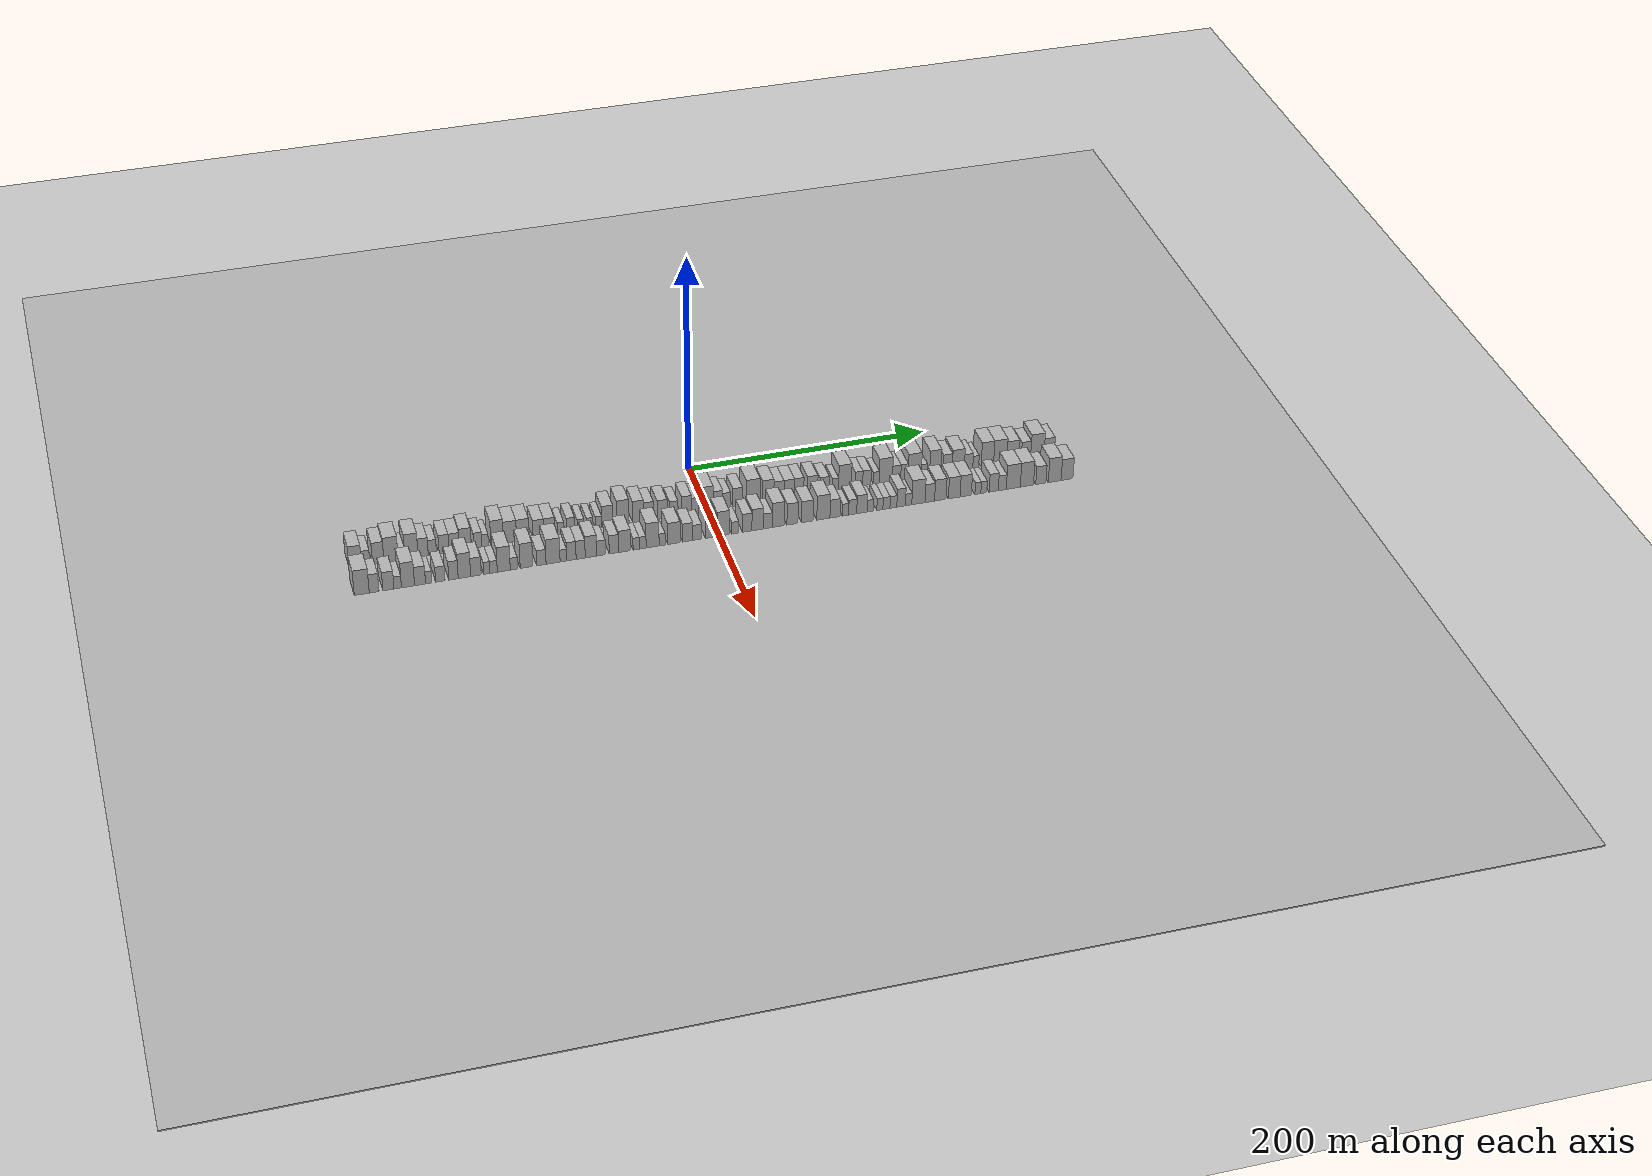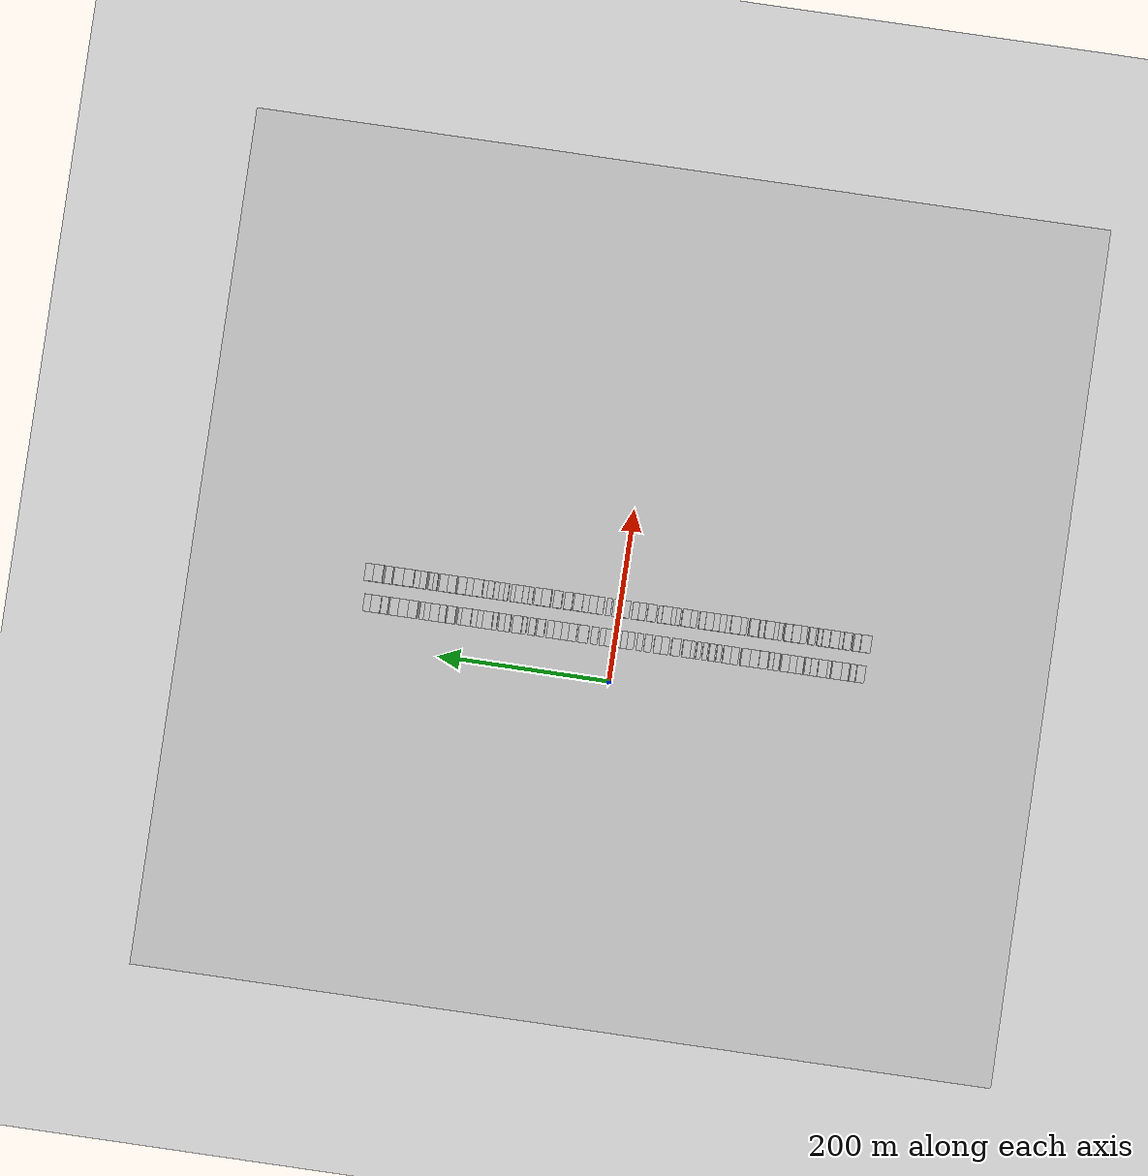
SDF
<?xml version="1.0" encoding="utf-8"?>

<sdf version="1.6">

   <world name="default">

      <gui fullscreen="0">

         <camera name="user_camera">

            <pose>-15 0 4.57585 0 0 0</pose>

            <view_controller>orbit</view_controller>

         </camera>

      </gui>

      <scene>

         <sky>

           <clouds>

             <speed>12</speed>

           </clouds>

         </sky>

         <ambient>0.4 0.4 0.4 1</ambient>

         <background>0.7 0.7 0.7 1</background>

         <shadows>1</shadows>

      </scene>

      <gravity>0 0 -9.8066</gravity>

      <magnetic_field>6e-06 2.3e-05 -4.2e-05</magnetic_field>

      <physics default="0" name="default_physics" type="ode">

         <ode>

            <solver>

               <type>quick</type>

               <iters>10</iters>

               <sor>1.0</sor>

               <use_dynamic_moi_rescaling>0</use_dynamic_moi_rescaling>

            </solver>

            <constraints>

               <cfm>0</cfm>

               <erp>0.2</erp>

               <contact_max_correcting_vel>100</contact_max_correcting_vel>

               <contact_surface_layer>0.001</contact_surface_layer>

            </constraints>

         </ode>

         <max_step_size>0.004</max_step_size>

         <real_time_factor>1</real_time_factor>

         <real_time_update_rate>250</real_time_update_rate>

      </physics>

      <light name="sun" type="directional">

         <cast_shadows>1</cast_shadows>

         <pose>0 0 10 0 0 0</pose>

         <diffuse>0.8 0.8 0.8 1</diffuse>

         <specular>0.2 0.2 0.2 1</specular>

         <attenuation>

            <range>1000</range>

            <constant>0.9</constant>

            <linear>0.01</linear>

            <quadratic>0.001</quadratic>

         </attenuation>

         <direction>-0.5 0.1 -0.9</direction>

      </light>

      <include>

         <name>ground_plane_1</name>

         <uri>model://HANNAS_ground_plane</uri>

         <pose>0 0 0  0 0 0</pose>

      </include>

      <include>

         <name>ground_plane_2</name>

         <uri>model://HANNAS_ground_plane</uri>

         <pose>100 0 0  0 0 0</pose>

      </include>

      <model name="building_1">

         <static>1</static>

         <pose frame="">50.0000 -283.1126 0 0.000000 0.000000 0.000000</pose>

         <link name="link">

            <pose frame="">0 0 10.50 0 0 0</pose>

            <collision name="collision">

               <geometry>

                  <box>

                     <size>20.0000 9.7748 21.0000</size>

                  </box>

               </geometry>

               <max_contacts>10</max_contacts>

               <surface>

                  <contact>

                     <ode/>

                  </contact>

                  <bounce/>

                  <friction>

                     <torsional>

                        <ode/>

                     </torsional>

                     <ode/>

                  </friction>

               </surface>

            </collision>

            <visual name="visual">

               <cast_shadows>0</cast_shadows>

               <geometry>

                  <box>

                     <size>20.0000 9.7748 21.0000</size>

                  </box>

               </geometry>

               <material>

                  <script>

                     <uri>model://HANNAS_wall/materials/scripts</uri>

                     <uri>model://HANNAS_wall/materials/textures</uri>

                     <name>vrc/HANNAS_wall</name>

                  </script>

               </material>

            </visual>

            <self_collide>0</self_collide>

            <enable_wind>0</enable_wind>

            <kinematic>0</kinematic>

         </link>

      </model>

      <model name="building_2">

         <static>1</static>

         <pose frame="">50.0000 -274.9102 0 0.000000 0.000000 0.000000</pose>

         <link name="link">

            <pose frame="">0 0 7.50 0 0 0</pose>

            <collision name="collision">

               <geometry>

                  <box>

                     <size>20.0000 6.6300 15.0000</size>

                  </box>

               </geometry>

               <max_contacts>10</max_contacts>

               <surface>

                  <contact>

                     <ode/>

                  </contact>

                  <bounce/>

                  <friction>

                     <torsional>

                        <ode/>

                     </torsional>

                     <ode/>

                  </friction>

               </surface>

            </collision>

            <visual name="visual">

               <cast_shadows>0</cast_shadows>

               <geometry>

                  <box>

                     <size>20.0000 6.6300 15.0000</size>

                  </box>

               </geometry>

               <material>

                  <script>

                     <uri>model://HANNAS_wall/materials/scripts</uri>

                     <uri>model://HANNAS_wall/materials/textures</uri>

                     <name>vrc/HANNAS_wall</name>

                  </script>

               </material>

            </visual>

            <self_collide>0</self_collide>

            <enable_wind>0</enable_wind>

            <kinematic>0</kinematic>

         </link>

      </model>

      <model name="building_3">

         <static>1</static>

         <pose frame="">50.0000 -265.1083 0 0.000000 0.000000 0.000000</pose>

         <link name="link">

            <pose frame="">0 0 10.50 0 0 0</pose>

            <collision name="collision">

               <geometry>

                  <box>

                     <size>20.0000 8.9737 21.0000</size>

                  </box>

               </geometry>

               <max_contacts>10</max_contacts>

               <surface>

                  <contact>

                     <ode/>

                  </contact>

                  <bounce/>

                  <friction>

                     <torsional>

                        <ode/>

                     </torsional>

                     <ode/>

                  </friction>

               </surface>

            </collision>

            <visual name="visual">

               <cast_shadows>0</cast_shadows>

               <geometry>

                  <box>

                     <size>20.0000 8.9737 21.0000</size>

                  </box>

               </geometry>

               <material>

                  <script>

                     <uri>model://HANNAS_wall/materials/scripts</uri>

                     <uri>model://HANNAS_wall/materials/textures</uri>

                     <name>vrc/HANNAS_wall</name>

                  </script>

               </material>

            </visual>

            <self_collide>0</self_collide>

            <enable_wind>0</enable_wind>

            <kinematic>0</kinematic>

         </link>

      </model>

      <model name="building_4">

         <static>1</static>

         <pose frame="">50.0000 -254.9887 0 0.000000 0.000000 0.000000</pose>

         <link name="link">

            <pose frame="">0 0 12.00 0 0 0</pose>

            <collision name="collision">

               <geometry>

                  <box>

                     <size>20.0000 11.2656 24.0000</size>

                  </box>

               </geometry>

               <max_contacts>10</max_contacts>

               <surface>

                  <contact>

                     <ode/>

                  </contact>

                  <bounce/>

                  <friction>

                     <torsional>

                        <ode/>

                     </torsional>

                     <ode/>

                  </friction>

               </surface>

            </collision>

            <visual name="visual">

               <cast_shadows>0</cast_shadows>

               <geometry>

                  <box>

                     <size>20.0000 11.2656 24.0000</size>

                  </box>

               </geometry>

               <material>

                  <script>

                     <uri>model://HANNAS_wall/materials/scripts</uri>

                     <uri>model://HANNAS_wall/materials/textures</uri>

                     <name>vrc/HANNAS_wall</name>

                  </script>

               </material>

            </visual>

            <self_collide>0</self_collide>

            <enable_wind>0</enable_wind>

            <kinematic>0</kinematic>

         </link>

      </model>

      <model name="building_5">

         <static>1</static>

         <pose frame="">50.0000 -246.7155 0 0.000000 0.000000 0.000000</pose>

         <link name="link">

            <pose frame="">0 0 6.00 0 0 0</pose>

            <collision name="collision">

               <geometry>

                  <box>

                     <size>20.0000 5.2808 12.0000</size>

                  </box>

               </geometry>

               <max_contacts>10</max_contacts>

               <surface>

                  <contact>

                     <ode/>

                  </contact>

                  <bounce/>

                  <friction>

                     <torsional>

                        <ode/>

                     </torsional>

                     <ode/>

                  </friction>

               </surface>

            </collision>

            <visual name="visual">

               <cast_shadows>0</cast_shadows>

               <geometry>

                  <box>

                     <size>20.0000 5.2808 12.0000</size>

                  </box>

               </geometry>

               <material>

                  <script>

                     <uri>model://HANNAS_wall/materials/scripts</uri>

                     <uri>model://HANNAS_wall/materials/textures</uri>

                     <name>vrc/HANNAS_wall</name>

                  </script>

               </material>

            </visual>

            <self_collide>0</self_collide>

            <enable_wind>0</enable_wind>

            <kinematic>0</kinematic>

         </link>

      </model>

      <model name="building_6">

         <static>1</static>

         <pose frame="">50.0000 -238.8820 0 0.000000 0.000000 0.000000</pose>

         <link name="link">

            <pose frame="">0 0 12.00 0 0 0</pose>

            <collision name="collision">

               <geometry>

                  <box>

                     <size>20.0000 10.3863 24.0000</size>

                  </box>

               </geometry>

               <max_contacts>10</max_contacts>

               <surface>

                  <contact>

                     <ode/>

                  </contact>

                  <bounce/>

                  <friction>

                     <torsional>

                        <ode/>

                     </torsional>

                     <ode/>

                  </friction>

               </surface>

            </collision>

            <visual name="visual">

               <cast_shadows>0</cast_shadows>

               <geometry>

                  <box>

                     <size>20.0000 10.3863 24.0000</size>

                  </box>

               </geometry>

               <material>

                  <script>

                     <uri>model://HANNAS_wall/materials/scripts</uri>

                     <uri>model://HANNAS_wall/materials/textures</uri>

                     <name>vrc/HANNAS_wall</name>

                  </script>

               </material>

            </visual>

            <self_collide>0</self_collide>

            <enable_wind>0</enable_wind>

            <kinematic>0</kinematic>

         </link>

      </model>

      <model name="building_7">

         <static>1</static>

         <pose frame="">50.0000 -229.6808 0 0.000000 0.000000 0.000000</pose>

         <link name="link">

            <pose frame="">0 0 9.00 0 0 0</pose>

            <collision name="collision">

               <geometry>

                  <box>

                     <size>20.0000 8.0159 18.0000</size>

                  </box>

               </geometry>

               <max_contacts>10</max_contacts>

               <surface>

                  <contact>

                     <ode/>

                  </contact>

                  <bounce/>

                  <friction>

                     <torsional>

                        <ode/>

                     </torsional>

                     <ode/>

                  </friction>

               </surface>

            </collision>

            <visual name="visual">

               <cast_shadows>0</cast_shadows>

               <geometry>

                  <box>

                     <size>20.0000 8.0159 18.0000</size>

                  </box>

               </geometry>

               <material>

                  <script>

                     <uri>model://HANNAS_wall/materials/scripts</uri>

                     <uri>model://HANNAS_wall/materials/textures</uri>

                     <name>vrc/HANNAS_wall</name>

                  </script>

               </material>

            </visual>

            <self_collide>0</self_collide>

            <enable_wind>0</enable_wind>

            <kinematic>0</kinematic>

         </link>

      </model>

      <model name="building_8">

         <static>1</static>

         <pose frame="">50.0000 -222.3984 0 0.000000 0.000000 0.000000</pose>

         <link name="link">

            <pose frame="">0 0 7.50 0 0 0</pose>

            <collision name="collision">

               <geometry>

                  <box>

                     <size>20.0000 6.5489 15.0000</size>

                  </box>

               </geometry>

               <max_contacts>10</max_contacts>

               <surface>

                  <contact>

                     <ode/>

                  </contact>

                  <bounce/>

                  <friction>

                     <torsional>

                        <ode/>

                     </torsional>

                     <ode/>

                  </friction>

               </surface>

            </collision>

            <visual name="visual">

               <cast_shadows>0</cast_shadows>

               <geometry>

                  <box>

                     <size>20.0000 6.5489 15.0000</size>

                  </box>

               </geometry>

               <material>

                  <script>

                     <uri>model://HANNAS_wall/materials/scripts</uri>

                     <uri>model://HANNAS_wall/materials/textures</uri>

                     <name>vrc/HANNAS_wall</name>

                  </script>

               </material>

            </visual>

            <self_collide>0</self_collide>

            <enable_wind>0</enable_wind>

            <kinematic>0</kinematic>

         </link>

      </model>

      <model name="building_9">

         <static>1</static>

         <pose frame="">50.0000 -213.1041 0 0.000000 0.000000 0.000000</pose>

         <link name="link">

            <pose frame="">0 0 9.00 0 0 0</pose>

            <collision name="collision">

               <geometry>

                  <box>

                     <size>20.0000 8.0398 18.0000</size>

                  </box>

               </geometry>

               <max_contacts>10</max_contacts>

               <surface>

                  <contact>

                     <ode/>

                  </contact>

                  <bounce/>

                  <friction>

                     <torsional>

                        <ode/>

                     </torsional>

                     <ode/>

                  </friction>

               </surface>

            </collision>

            <visual name="visual">

               <cast_shadows>0</cast_shadows>

               <geometry>

                  <box>

                     <size>20.0000 8.0398 18.0000</size>

                  </box>

               </geometry>

               <material>

                  <script>

                     <uri>model://HANNAS_wall/materials/scripts</uri>

                     <uri>model://HANNAS_wall/materials/textures</uri>

                     <name>vrc/HANNAS_wall</name>

                  </script>

               </material>

            </visual>

            <self_collide>0</self_collide>

            <enable_wind>0</enable_wind>

            <kinematic>0</kinematic>

         </link>

      </model>

      <model name="building_10">

         <static>1</static>

         <pose frame="">50.0000 -204.9203 0 0.000000 0.000000 0.000000</pose>

         <link name="link">

            <pose frame="">0 0 9.00 0 0 0</pose>

            <collision name="collision">

               <geometry>

                  <box>

                     <size>20.0000 8.3279 18.0000</size>

                  </box>

               </geometry>

               <max_contacts>10</max_contacts>

               <surface>

                  <contact>

                     <ode/>

                  </contact>

                  <bounce/>

                  <friction>

                     <torsional>

                        <ode/>

                     </torsional>

                     <ode/>

                  </friction>

               </surface>

            </collision>

            <visual name="visual">

               <cast_shadows>0</cast_shadows>

               <geometry>

                  <box>

                     <size>20.0000 8.3279 18.0000</size>

                  </box>

               </geometry>

               <material>

                  <script>

                     <uri>model://HANNAS_wall/materials/scripts</uri>

                     <uri>model://HANNAS_wall/materials/textures</uri>

                     <name>vrc/HANNAS_wall</name>

                  </script>

               </material>

            </visual>

            <self_collide>0</self_collide>

            <enable_wind>0</enable_wind>

            <kinematic>0</kinematic>

         </link>

      </model>

      <model name="building_11">

         <static>1</static>

         <pose frame="">50.0000 -196.1393 0 0.000000 0.000000 0.000000</pose>

         <link name="link">

            <pose frame="">0 0 10.50 0 0 0</pose>

            <collision name="collision">

               <geometry>

                  <box>

                     <size>20.0000 9.2340 21.0000</size>

                  </box>

               </geometry>

               <max_contacts>10</max_contacts>

               <surface>

                  <contact>

                     <ode/>

                  </contact>

                  <bounce/>

                  <friction>

                     <torsional>

                        <ode/>

                     </torsional>

                     <ode/>

                  </friction>

               </surface>

            </collision>

            <visual name="visual">

               <cast_shadows>0</cast_shadows>

               <geometry>

                  <box>

                     <size>20.0000 9.2340 21.0000</size>

                  </box>

               </geometry>

               <material>

                  <script>

                     <uri>model://HANNAS_wall/materials/scripts</uri>

                     <uri>model://HANNAS_wall/materials/textures</uri>

                     <name>vrc/HANNAS_wall</name>

                  </script>

               </material>

            </visual>

            <self_collide>0</self_collide>

            <enable_wind>0</enable_wind>

            <kinematic>0</kinematic>

         </link>

      </model>

      <model name="building_12">

         <static>1</static>

         <pose frame="">50.0000 -186.2791 0 0.000000 0.000000 0.000000</pose>

         <link name="link">

            <pose frame="">0 0 7.50 0 0 0</pose>

            <collision name="collision">

               <geometry>

                  <box>

                     <size>20.0000 6.4864 15.0000</size>

                  </box>

               </geometry>

               <max_contacts>10</max_contacts>

               <surface>

                  <contact>

                     <ode/>

                  </contact>

                  <bounce/>

                  <friction>

                     <torsional>

                        <ode/>

                     </torsional>

                     <ode/>

                  </friction>

               </surface>

            </collision>

            <visual name="visual">

               <cast_shadows>0</cast_shadows>

               <geometry>

                  <box>

                     <size>20.0000 6.4864 15.0000</size>

                  </box>

               </geometry>

               <material>

                  <script>

                     <uri>model://HANNAS_wall/materials/scripts</uri>

                     <uri>model://HANNAS_wall/materials/textures</uri>

                     <name>vrc/HANNAS_wall</name>

                  </script>

               </material>

            </visual>

            <self_collide>0</self_collide>

            <enable_wind>0</enable_wind>

            <kinematic>0</kinematic>

         </link>

      </model>

      <model name="building_13">

         <static>1</static>

         <pose frame="">50.0000 -180.4282 0 0.000000 0.000000 0.000000</pose>

         <link name="link">

            <pose frame="">0 0 6.00 0 0 0</pose>

            <collision name="collision">

               <geometry>

                  <box>

                     <size>20.0000 5.2154 12.0000</size>

                  </box>

               </geometry>

               <max_contacts>10</max_contacts>

               <surface>

                  <contact>

                     <ode/>

                  </contact>

                  <bounce/>

                  <friction>

                     <torsional>

                        <ode/>

                     </torsional>

                     <ode/>

                  </friction>

               </surface>

            </collision>

            <visual name="visual">

               <cast_shadows>0</cast_shadows>

               <geometry>

                  <box>

                     <size>20.0000 5.2154 12.0000</size>

                  </box>

               </geometry>

               <material>

                  <script>

                     <uri>model://HANNAS_wall/materials/scripts</uri>

                     <uri>model://HANNAS_wall/materials/textures</uri>

                     <name>vrc/HANNAS_wall</name>

                  </script>

               </material>

            </visual>

            <self_collide>0</self_collide>

            <enable_wind>0</enable_wind>

            <kinematic>0</kinematic>

         </link>

      </model>

      <model name="building_14">

         <static>1</static>

         <pose frame="">50.0000 -170.7632 0 0.000000 0.000000 0.000000</pose>

         <link name="link">

            <pose frame="">0 0 12.00 0 0 0</pose>

            <collision name="collision">

               <geometry>

                  <box>

                     <size>20.0000 10.1147 24.0000</size>

                  </box>

               </geometry>

               <max_contacts>10</max_contacts>

               <surface>

                  <contact>

                     <ode/>

                  </contact>

                  <bounce/>

                  <friction>

                     <torsional>

                        <ode/>

                     </torsional>

                     <ode/>

                  </friction>

               </surface>

            </collision>

            <visual name="visual">

               <cast_shadows>0</cast_shadows>

               <geometry>

                  <box>

                     <size>20.0000 10.1147 24.0000</size>

                  </box>

               </geometry>

               <material>

                  <script>

                     <uri>model://HANNAS_wall/materials/scripts</uri>

                     <uri>model://HANNAS_wall/materials/textures</uri>

                     <name>vrc/HANNAS_wall</name>

                  </script>

               </material>

            </visual>

            <self_collide>0</self_collide>

            <enable_wind>0</enable_wind>

            <kinematic>0</kinematic>

         </link>

      </model>

      <model name="building_15">

         <static>1</static>

         <pose frame="">50.0000 -160.4710 0 0.000000 0.000000 0.000000</pose>

         <link name="link">

            <pose frame="">0 0 10.50 0 0 0</pose>

            <collision name="collision">

               <geometry>

                  <box>

                     <size>20.0000 10.4697 21.0000</size>

                  </box>

               </geometry>

               <max_contacts>10</max_contacts>

               <surface>

                  <contact>

                     <ode/>

                  </contact>

                  <bounce/>

                  <friction>

                     <torsional>

                        <ode/>

                     </torsional>

                     <ode/>

                  </friction>

               </surface>

            </collision>

            <visual name="visual">

               <cast_shadows>0</cast_shadows>

               <geometry>

                  <box>

                     <size>20.0000 10.4697 21.0000</size>

                  </box>

               </geometry>

               <material>

                  <script>

                     <uri>model://HANNAS_wall/materials/scripts</uri>

                     <uri>model://HANNAS_wall/materials/textures</uri>

                     <name>vrc/HANNAS_wall</name>

                  </script>

               </material>

            </visual>

            <self_collide>0</self_collide>

            <enable_wind>0</enable_wind>

            <kinematic>0</kinematic>

         </link>

      </model>

      <model name="building_16">

         <static>1</static>

         <pose frame="">50.0000 -150.1489 0 0.000000 0.000000 0.000000</pose>

         <link name="link">

            <pose frame="">0 0 10.50 0 0 0</pose>

            <collision name="collision">

               <geometry>

                  <box>

                     <size>20.0000 10.1744 21.0000</size>

                  </box>

               </geometry>

               <max_contacts>10</max_contacts>

               <surface>

                  <contact>

                     <ode/>

                  </contact>

                  <bounce/>

                  <friction>

                     <torsional>

                        <ode/>

                     </torsional>

                     <ode/>

                  </friction>

               </surface>

            </collision>

            <visual name="visual">

               <cast_shadows>0</cast_shadows>

               <geometry>

                  <box>

                     <size>20.0000 10.1744 21.0000</size>

                  </box>

               </geometry>

               <material>

                  <script>

                     <uri>model://HANNAS_wall/materials/scripts</uri>

                     <uri>model://HANNAS_wall/materials/textures</uri>

                     <name>vrc/HANNAS_wall</name>

                  </script>

               </material>

            </visual>

            <self_collide>0</self_collide>

            <enable_wind>0</enable_wind>

            <kinematic>0</kinematic>

         </link>

      </model>

      <model name="building_17">

         <static>1</static>

         <pose frame="">50.0000 -137.6509 0 0.000000 0.000000 0.000000</pose>

         <link name="link">

            <pose frame="">0 0 9.00 0 0 0</pose>

            <collision name="collision">

               <geometry>

                  <box>

                     <size>20.0000 8.8214 18.0000</size>

                  </box>

               </geometry>

               <max_contacts>10</max_contacts>

               <surface>

                  <contact>

                     <ode/>

                  </contact>

                  <bounce/>

                  <friction>

                     <torsional>

                        <ode/>

                     </torsional>

                     <ode/>

                  </friction>

               </surface>

            </collision>

            <visual name="visual">

               <cast_shadows>0</cast_shadows>

               <geometry>

                  <box>

                     <size>20.0000 8.8214 18.0000</size>

                  </box>

               </geometry>

               <material>

                  <script>

                     <uri>model://HANNAS_wall/materials/scripts</uri>

                     <uri>model://HANNAS_wall/materials/textures</uri>

                     <name>vrc/HANNAS_wall</name>

                  </script>

               </material>

            </visual>

            <self_collide>0</self_collide>

            <enable_wind>0</enable_wind>

            <kinematic>0</kinematic>

         </link>

      </model>

      <model name="building_18">

         <static>1</static>

         <pose frame="">50.0000 -128.8760 0 0.000000 0.000000 0.000000</pose>

         <link name="link">

            <pose frame="">0 0 9.00 0 0 0</pose>

            <collision name="collision">

               <geometry>

                  <box>

                     <size>20.0000 8.7284 18.0000</size>

                  </box>

               </geometry>

               <max_contacts>10</max_contacts>

               <surface>

                  <contact>

                     <ode/>

                  </contact>

                  <bounce/>

                  <friction>

                     <torsional>

                        <ode/>

                     </torsional>

                     <ode/>

                  </friction>

               </surface>

            </collision>

            <visual name="visual">

               <cast_shadows>0</cast_shadows>

               <geometry>

                  <box>

                     <size>20.0000 8.7284 18.0000</size>

                  </box>

               </geometry>

               <material>

                  <script>

                     <uri>model://HANNAS_wall/materials/scripts</uri>

                     <uri>model://HANNAS_wall/materials/textures</uri>

                     <name>vrc/HANNAS_wall</name>

                  </script>

               </material>

            </visual>

            <self_collide>0</self_collide>

            <enable_wind>0</enable_wind>

            <kinematic>0</kinematic>

         </link>

      </model>

      <model name="building_19">

         <static>1</static>

         <pose frame="">50.0000 -119.8155 0 0.000000 0.000000 0.000000</pose>

         <link name="link">

            <pose frame="">0 0 6.00 0 0 0</pose>

            <collision name="collision">

               <geometry>

                  <box>

                     <size>20.0000 5.3927 12.0000</size>

                  </box>

               </geometry>

               <max_contacts>10</max_contacts>

               <surface>

                  <contact>

                     <ode/>

                  </contact>

                  <bounce/>

                  <friction>

                     <torsional>

                        <ode/>

                     </torsional>

                     <ode/>

                  </friction>

               </surface>

            </collision>

            <visual name="visual">

               <cast_shadows>0</cast_shadows>

               <geometry>

                  <box>

                     <size>20.0000 5.3927 12.0000</size>

                  </box>

               </geometry>

               <material>

                  <script>

                     <uri>model://HANNAS_wall/materials/scripts</uri>

                     <uri>model://HANNAS_wall/materials/textures</uri>

                     <name>vrc/HANNAS_wall</name>

                  </script>

               </material>

            </visual>

            <self_collide>0</self_collide>

            <enable_wind>0</enable_wind>

            <kinematic>0</kinematic>

         </link>

      </model>

      <model name="building_20">

         <static>1</static>

         <pose frame="">50.0000 -111.7386 0 0.000000 0.000000 0.000000</pose>

         <link name="link">

            <pose frame="">0 0 7.50 0 0 0</pose>

            <collision name="collision">

               <geometry>

                  <box>

                     <size>20.0000 6.7611 15.0000</size>

                  </box>

               </geometry>

               <max_contacts>10</max_contacts>

               <surface>

                  <contact>

                     <ode/>

                  </contact>

                  <bounce/>

                  <friction>

                     <torsional>

                        <ode/>

                     </torsional>

                     <ode/>

                  </friction>

               </surface>

            </collision>

            <visual name="visual">

               <cast_shadows>0</cast_shadows>

               <geometry>

                  <box>

                     <size>20.0000 6.7611 15.0000</size>

                  </box>

               </geometry>

               <material>

                  <script>

                     <uri>model://HANNAS_wall/materials/scripts</uri>

                     <uri>model://HANNAS_wall/materials/textures</uri>

                     <name>vrc/HANNAS_wall</name>

                  </script>

               </material>

            </visual>

            <self_collide>0</self_collide>

            <enable_wind>0</enable_wind>

            <kinematic>0</kinematic>

         </link>

      </model>

      <model name="building_21">

         <static>1</static>

         <pose frame="">50.0000 -103.6597 0 0.000000 0.000000 0.000000</pose>

         <link name="link">

            <pose frame="">0 0 6.00 0 0 0</pose>

            <collision name="collision">

               <geometry>

                  <box>

                     <size>20.0000 5.3967 12.0000</size>

                  </box>

               </geometry>

               <max_contacts>10</max_contacts>

               <surface>

                  <contact>

                     <ode/>

                  </contact>

                  <bounce/>

                  <friction>

                     <torsional>

                        <ode/>

                     </torsional>

                     <ode/>

                  </friction>

               </surface>

            </collision>

            <visual name="visual">

               <cast_shadows>0</cast_shadows>

               <geometry>

                  <box>

                     <size>20.0000 5.3967 12.0000</size>

                  </box>

               </geometry>

               <material>

                  <script>

                     <uri>model://HANNAS_wall/materials/scripts</uri>

                     <uri>model://HANNAS_wall/materials/textures</uri>

                     <name>vrc/HANNAS_wall</name>

                  </script>

               </material>

            </visual>

            <self_collide>0</self_collide>

            <enable_wind>0</enable_wind>

            <kinematic>0</kinematic>

         </link>

      </model>

      <model name="building_22">

         <static>1</static>

         <pose frame="">50.0000 -96.3648 0 0.000000 0.000000 0.000000</pose>

         <link name="link">

            <pose frame="">0 0 6.00 0 0 0</pose>

            <collision name="collision">

               <geometry>

                  <box>

                     <size>20.0000 5.1931 12.0000</size>

                  </box>

               </geometry>

               <max_contacts>10</max_contacts>

               <surface>

                  <contact>

                     <ode/>

                  </contact>

                  <bounce/>

                  <friction>

                     <torsional>

                        <ode/>

                     </torsional>

                     <ode/>

                  </friction>

               </surface>

            </collision>

            <visual name="visual">

               <cast_shadows>0</cast_shadows>

               <geometry>

                  <box>

                     <size>20.0000 5.1931 12.0000</size>

                  </box>

               </geometry>

               <material>

                  <script>

                     <uri>model://HANNAS_wall/materials/scripts</uri>

                     <uri>model://HANNAS_wall/materials/textures</uri>

                     <name>vrc/HANNAS_wall</name>

                  </script>

               </material>

            </visual>

            <self_collide>0</self_collide>

            <enable_wind>0</enable_wind>

            <kinematic>0</kinematic>

         </link>

      </model>

      <model name="building_23">

         <static>1</static>

         <pose frame="">50.0000 -89.1910 0 0.000000 0.000000 0.000000</pose>

         <link name="link">

            <pose frame="">0 0 6.00 0 0 0</pose>

            <collision name="collision">

               <geometry>

                  <box>

                     <size>20.0000 5.1546 12.0000</size>

                  </box>

               </geometry>

               <max_contacts>10</max_contacts>

               <surface>

                  <contact>

                     <ode/>

                  </contact>

                  <bounce/>

                  <friction>

                     <torsional>

                        <ode/>

                     </torsional>

                     <ode/>

                  </friction>

               </surface>

            </collision>

            <visual name="visual">

               <cast_shadows>0</cast_shadows>

               <geometry>

                  <box>

                     <size>20.0000 5.1546 12.0000</size>

                  </box>

               </geometry>

               <material>

                  <script>

                     <uri>model://HANNAS_wall/materials/scripts</uri>

                     <uri>model://HANNAS_wall/materials/textures</uri>

                     <name>vrc/HANNAS_wall</name>

                  </script>

               </material>

            </visual>

            <self_collide>0</self_collide>

            <enable_wind>0</enable_wind>

            <kinematic>0</kinematic>

         </link>

      </model>

      <model name="building_24">

         <static>1</static>

         <pose frame="">50.0000 -82.0602 0 0.000000 0.000000 0.000000</pose>

         <link name="link">

            <pose frame="">0 0 10.50 0 0 0</pose>

            <collision name="collision">

               <geometry>

                  <box>

                     <size>20.0000 9.1070 21.0000</size>

                  </box>

               </geometry>

               <max_contacts>10</max_contacts>

               <surface>

                  <contact>

                     <ode/>

                  </contact>

                  <bounce/>

                  <friction>

                     <torsional>

                        <ode/>

                     </torsional>

                     <ode/>

                  </friction>

               </surface>

            </collision>

            <visual name="visual">

               <cast_shadows>0</cast_shadows>

               <geometry>

                  <box>

                     <size>20.0000 9.1070 21.0000</size>

                  </box>

               </geometry>

               <material>

                  <script>

                     <uri>model://HANNAS_wall/materials/scripts</uri>

                     <uri>model://HANNAS_wall/materials/textures</uri>

                     <name>vrc/HANNAS_wall</name>

                  </script>

               </material>

            </visual>

            <self_collide>0</self_collide>

            <enable_wind>0</enable_wind>

            <kinematic>0</kinematic>

         </link>

      </model>

      <model name="building_25">

         <static>1</static>

         <pose frame="">50.0000 -69.5105 0 0.000000 0.000000 0.000000</pose>

         <link name="link">

            <pose frame="">0 0 12.00 0 0 0</pose>

            <collision name="collision">

               <geometry>

                  <box>

                     <size>20.0000 9.9925 24.0000</size>

                  </box>

               </geometry>

               <max_contacts>10</max_contacts>

               <surface>

                  <contact>

                     <ode/>

                  </contact>

                  <bounce/>

                  <friction>

                     <torsional>

                        <ode/>

                     </torsional>

                     <ode/>

                  </friction>

               </surface>

            </collision>

            <visual name="visual">

               <cast_shadows>0</cast_shadows>

               <geometry>

                  <box>

                     <size>20.0000 9.9925 24.0000</size>

                  </box>

               </geometry>

               <material>

                  <script>

                     <uri>model://HANNAS_wall/materials/scripts</uri>

                     <uri>model://HANNAS_wall/materials/textures</uri>

                     <name>vrc/HANNAS_wall</name>

                  </script>

               </material>

            </visual>

            <self_collide>0</self_collide>

            <enable_wind>0</enable_wind>

            <kinematic>0</kinematic>

         </link>

      </model>

      <model name="building_26">

         <static>1</static>

         <pose frame="">50.0000 -57.0944 0 0.000000 0.000000 0.000000</pose>

         <link name="link">

            <pose frame="">0 0 10.50 0 0 0</pose>

            <collision name="collision">

               <geometry>

                  <box>

                     <size>20.0000 8.8398 21.0000</size>

                  </box>

               </geometry>

               <max_contacts>10</max_contacts>

               <surface>

                  <contact>

                     <ode/>

                  </contact>

                  <bounce/>

                  <friction>

                     <torsional>

                        <ode/>

                     </torsional>

                     <ode/>

                  </friction>

               </surface>

            </collision>

            <visual name="visual">

               <cast_shadows>0</cast_shadows>

               <geometry>

                  <box>

                     <size>20.0000 8.8398 21.0000</size>

                  </box>

               </geometry>

               <material>

                  <script>

                     <uri>model://HANNAS_wall/materials/scripts</uri>

                     <uri>model://HANNAS_wall/materials/textures</uri>

                     <name>vrc/HANNAS_wall</name>

                  </script>

               </material>

            </visual>

            <self_collide>0</self_collide>

            <enable_wind>0</enable_wind>

            <kinematic>0</kinematic>

         </link>

      </model>

      <model name="building_27">

         <static>1</static>

         <pose frame="">50.0000 -48.5815 0 0.000000 0.000000 0.000000</pose>

         <link name="link">

            <pose frame="">0 0 9.00 0 0 0</pose>

            <collision name="collision">

               <geometry>

                  <box>

                     <size>20.0000 8.1859 18.0000</size>

                  </box>

               </geometry>

               <max_contacts>10</max_contacts>

               <surface>

                  <contact>

                     <ode/>

                  </contact>

                  <bounce/>

                  <friction>

                     <torsional>

                        <ode/>

                     </torsional>

                     <ode/>

                  </friction>

               </surface>

            </collision>

            <visual name="visual">

               <cast_shadows>0</cast_shadows>

               <geometry>

                  <box>

                     <size>20.0000 8.1859 18.0000</size>

                  </box>

               </geometry>

               <material>

                  <script>

                     <uri>model://HANNAS_wall/materials/scripts</uri>

                     <uri>model://HANNAS_wall/materials/textures</uri>

                     <name>vrc/HANNAS_wall</name>

                  </script>

               </material>

            </visual>

            <self_collide>0</self_collide>

            <enable_wind>0</enable_wind>

            <kinematic>0</kinematic>

         </link>

      </model>

      <model name="building_28">

         <static>1</static>

         <pose frame="">50.0000 -37.4113 0 0.000000 0.000000 0.000000</pose>

         <link name="link">

            <pose frame="">0 0 9.00 0 0 0</pose>

            <collision name="collision">

               <geometry>

                  <box>

                     <size>20.0000 8.1546 18.0000</size>

                  </box>

               </geometry>

               <max_contacts>10</max_contacts>

               <surface>

                  <contact>

                     <ode/>

                  </contact>

                  <bounce/>

                  <friction>

                     <torsional>

                        <ode/>

                     </torsional>

                     <ode/>

                  </friction>

               </surface>

            </collision>

            <visual name="visual">

               <cast_shadows>0</cast_shadows>

               <geometry>

                  <box>

                     <size>20.0000 8.1546 18.0000</size>

                  </box>

               </geometry>

               <material>

                  <script>

                     <uri>model://HANNAS_wall/materials/scripts</uri>

                     <uri>model://HANNAS_wall/materials/textures</uri>

                     <name>vrc/HANNAS_wall</name>

                  </script>

               </material>

            </visual>

            <self_collide>0</self_collide>

            <enable_wind>0</enable_wind>

            <kinematic>0</kinematic>

         </link>

      </model>

      <model name="building_29">

         <static>1</static>

         <pose frame="">50.0000 -27.9092 0 0.000000 0.000000 0.000000</pose>

         <link name="link">

            <pose frame="">0 0 7.50 0 0 0</pose>

            <collision name="collision">

               <geometry>

                  <box>

                     <size>20.0000 6.8497 15.0000</size>

                  </box>

               </geometry>

               <max_contacts>10</max_contacts>

               <surface>

                  <contact>

                     <ode/>

                  </contact>

                  <bounce/>

                  <friction>

                     <torsional>

                        <ode/>

                     </torsional>

                     <ode/>

                  </friction>

               </surface>

            </collision>

            <visual name="visual">

               <cast_shadows>0</cast_shadows>

               <geometry>

                  <box>

                     <size>20.0000 6.8497 15.0000</size>

                  </box>

               </geometry>

               <material>

                  <script>

                     <uri>model://HANNAS_wall/materials/scripts</uri>

                     <uri>model://HANNAS_wall/materials/textures</uri>

                     <name>vrc/HANNAS_wall</name>

                  </script>

               </material>

            </visual>

            <self_collide>0</self_collide>

            <enable_wind>0</enable_wind>

            <kinematic>0</kinematic>

         </link>

      </model>

      <model name="building_30">

         <static>1</static>

         <pose frame="">50.0000 -17.4565 0 0.000000 0.000000 0.000000</pose>

         <link name="link">

            <pose frame="">0 0 9.00 0 0 0</pose>

            <collision name="collision">

               <geometry>

                  <box>

                     <size>20.0000 8.0557 18.0000</size>

                  </box>

               </geometry>

               <max_contacts>10</max_contacts>

               <surface>

                  <contact>

                     <ode/>

                  </contact>

                  <bounce/>

                  <friction>

                     <torsional>

                        <ode/>

                     </torsional>

                     <ode/>

                  </friction>

               </surface>

            </collision>

            <visual name="visual">

               <cast_shadows>0</cast_shadows>

               <geometry>

                  <box>

                     <size>20.0000 8.0557 18.0000</size>

                  </box>

               </geometry>

               <material>

                  <script>

                     <uri>model://HANNAS_wall/materials/scripts</uri>

                     <uri>model://HANNAS_wall/materials/textures</uri>

                     <name>vrc/HANNAS_wall</name>

                  </script>

               </material>

            </visual>

            <self_collide>0</self_collide>

            <enable_wind>0</enable_wind>

            <kinematic>0</kinematic>

         </link>

      </model>

      <model name="building_31">

         <static>1</static>

         <pose frame="">50.0000 -9.7898 0 0.000000 0.000000 0.000000</pose>

         <link name="link">

            <pose frame="">0 0 7.50 0 0 0</pose>

            <collision name="collision">

               <geometry>

                  <box>

                     <size>20.0000 7.2776 15.0000</size>

                  </box>

               </geometry>

               <max_contacts>10</max_contacts>

               <surface>

                  <contact>

                     <ode/>

                  </contact>

                  <bounce/>

                  <friction>

                     <torsional>

                        <ode/>

                     </torsional>

                     <ode/>

                  </friction>

               </surface>

            </collision>

            <visual name="visual">

               <cast_shadows>0</cast_shadows>

               <geometry>

                  <box>

                     <size>20.0000 7.2776 15.0000</size>

                  </box>

               </geometry>

               <material>

                  <script>

                     <uri>model://HANNAS_wall/materials/scripts</uri>

                     <uri>model://HANNAS_wall/materials/textures</uri>

                     <name>vrc/HANNAS_wall</name>

                  </script>

               </material>

            </visual>

            <self_collide>0</self_collide>

            <enable_wind>0</enable_wind>

            <kinematic>0</kinematic>

         </link>

      </model>

      <model name="building_32">

         <static>1</static>

         <pose frame="">50.0000 -0.8902 0 0.000000 0.000000 0.000000</pose>

         <link name="link">

            <pose frame="">0 0 12.00 0 0 0</pose>

            <collision name="collision">

               <geometry>

                  <box>

                     <size>20.0000 10.5216 24.0000</size>

                  </box>

               </geometry>

               <max_contacts>10</max_contacts>

               <surface>

                  <contact>

                     <ode/>

                  </contact>

                  <bounce/>

                  <friction>

                     <torsional>

                        <ode/>

                     </torsional>

                     <ode/>

                  </friction>

               </surface>

            </collision>

            <visual name="visual">

               <cast_shadows>0</cast_shadows>

               <geometry>

                  <box>

                     <size>20.0000 10.5216 24.0000</size>

                  </box>

               </geometry>

               <material>

                  <script>

                     <uri>model://HANNAS_wall/materials/scripts</uri>

                     <uri>model://HANNAS_wall/materials/textures</uri>

                     <name>vrc/HANNAS_wall</name>

                  </script>

               </material>

            </visual>

            <self_collide>0</self_collide>

            <enable_wind>0</enable_wind>

            <kinematic>0</kinematic>

         </link>

      </model>

      <model name="building_33">

         <static>1</static>

         <pose frame="">50.0000 8.3077 0 0.000000 0.000000 0.000000</pose>

         <link name="link">

            <pose frame="">0 0 9.00 0 0 0</pose>

            <collision name="collision">

               <geometry>

                  <box>

                     <size>20.0000 7.8744 18.0000</size>

                  </box>

               </geometry>

               <max_contacts>10</max_contacts>

               <surface>

                  <contact>

                     <ode/>

                  </contact>

                  <bounce/>

                  <friction>

                     <torsional>

                        <ode/>

                     </torsional>

                     <ode/>

                  </friction>

               </surface>

            </collision>

            <visual name="visual">

               <cast_shadows>0</cast_shadows>

               <geometry>

                  <box>

                     <size>20.0000 7.8744 18.0000</size>

                  </box>

               </geometry>

               <material>

                  <script>

                     <uri>model://HANNAS_wall/materials/scripts</uri>

                     <uri>model://HANNAS_wall/materials/textures</uri>

                     <name>vrc/HANNAS_wall</name>

                  </script>

               </material>

            </visual>

            <self_collide>0</self_collide>

            <enable_wind>0</enable_wind>

            <kinematic>0</kinematic>

         </link>

      </model>

      <model name="building_34">

         <static>1</static>

         <pose frame="">50.0000 15.4717 0 0.000000 0.000000 0.000000</pose>

         <link name="link">

            <pose frame="">0 0 7.50 0 0 0</pose>

            <collision name="collision">

               <geometry>

                  <box>

                     <size>20.0000 6.4537 15.0000</size>

                  </box>

               </geometry>

               <max_contacts>10</max_contacts>

               <surface>

                  <contact>

                     <ode/>

                  </contact>

                  <bounce/>

                  <friction>

                     <torsional>

                        <ode/>

                     </torsional>

                     <ode/>

                  </friction>

               </surface>

            </collision>

            <visual name="visual">

               <cast_shadows>0</cast_shadows>

               <geometry>

                  <box>

                     <size>20.0000 6.4537 15.0000</size>

                  </box>

               </geometry>

               <material>

                  <script>

                     <uri>model://HANNAS_wall/materials/scripts</uri>

                     <uri>model://HANNAS_wall/materials/textures</uri>

                     <name>vrc/HANNAS_wall</name>

                  </script>

               </material>

            </visual>

            <self_collide>0</self_collide>

            <enable_wind>0</enable_wind>

            <kinematic>0</kinematic>

         </link>

      </model>

      <model name="building_35">

         <static>1</static>

         <pose frame="">50.0000 24.6957 0 0.000000 0.000000 0.000000</pose>

         <link name="link">

            <pose frame="">0 0 9.00 0 0 0</pose>

            <collision name="collision">

               <geometry>

                  <box>

                     <size>20.0000 7.9942 18.0000</size>

                  </box>

               </geometry>

               <max_contacts>10</max_contacts>

               <surface>

                  <contact>

                     <ode/>

                  </contact>

                  <bounce/>

                  <friction>

                     <torsional>

                        <ode/>

                     </torsional>

                     <ode/>

                  </friction>

               </surface>

            </collision>

            <visual name="visual">

               <cast_shadows>0</cast_shadows>

               <geometry>

                  <box>

                     <size>20.0000 7.9942 18.0000</size>

                  </box>

               </geometry>

               <material>

                  <script>

                     <uri>model://HANNAS_wall/materials/scripts</uri>

                     <uri>model://HANNAS_wall/materials/textures</uri>

                     <name>vrc/HANNAS_wall</name>

                  </script>

               </material>

            </visual>

            <self_collide>0</self_collide>

            <enable_wind>0</enable_wind>

            <kinematic>0</kinematic>

         </link>

      </model>

      <model name="building_36">

         <static>1</static>

         <pose frame="">50.0000 37.4845 0 0.000000 0.000000 0.000000</pose>

         <link name="link">

            <pose frame="">0 0 12.00 0 0 0</pose>

            <collision name="collision">

               <geometry>

                  <box>

                     <size>20.0000 11.5835 24.0000</size>

                  </box>

               </geometry>

               <max_contacts>10</max_contacts>

               <surface>

                  <contact>

                     <ode/>

                  </contact>

                  <bounce/>

                  <friction>

                     <torsional>

                        <ode/>

                     </torsional>

                     <ode/>

                  </friction>

               </surface>

            </collision>

            <visual name="visual">

               <cast_shadows>0</cast_shadows>

               <geometry>

                  <box>

                     <size>20.0000 11.5835 24.0000</size>

                  </box>

               </geometry>

               <material>

                  <script>

                     <uri>model://HANNAS_wall/materials/scripts</uri>

                     <uri>model://HANNAS_wall/materials/textures</uri>

                     <name>vrc/HANNAS_wall</name>

                  </script>

               </material>

            </visual>

            <self_collide>0</self_collide>

            <enable_wind>0</enable_wind>

            <kinematic>0</kinematic>

         </link>

      </model>

      <model name="building_37">

         <static>1</static>

         <pose frame="">50.0000 49.9310 0 0.000000 0.000000 0.000000</pose>

         <link name="link">

            <pose frame="">0 0 10.50 0 0 0</pose>

            <collision name="collision">

               <geometry>

                  <box>

                     <size>20.0000 9.3095 21.0000</size>

                  </box>

               </geometry>

               <max_contacts>10</max_contacts>

               <surface>

                  <contact>

                     <ode/>

                  </contact>

                  <bounce/>

                  <friction>

                     <torsional>

                        <ode/>

                     </torsional>

                     <ode/>

                  </friction>

               </surface>

            </collision>

            <visual name="visual">

               <cast_shadows>0</cast_shadows>

               <geometry>

                  <box>

                     <size>20.0000 9.3095 21.0000</size>

                  </box>

               </geometry>

               <material>

                  <script>

                     <uri>model://HANNAS_wall/materials/scripts</uri>

                     <uri>model://HANNAS_wall/materials/textures</uri>

                     <name>vrc/HANNAS_wall</name>

                  </script>

               </material>

            </visual>

            <self_collide>0</self_collide>

            <enable_wind>0</enable_wind>

            <kinematic>0</kinematic>

         </link>

      </model>

      <model name="building_38">

         <static>1</static>

         <pose frame="">50.0000 58.7630 0 0.000000 0.000000 0.000000</pose>

         <link name="link">

            <pose frame="">0 0 9.00 0 0 0</pose>

            <collision name="collision">

               <geometry>

                  <box>

                     <size>20.0000 8.3544 18.0000</size>

                  </box>

               </geometry>

               <max_contacts>10</max_contacts>

               <surface>

                  <contact>

                     <ode/>

                  </contact>

                  <bounce/>

                  <friction>

                     <torsional>

                        <ode/>

                     </torsional>

                     <ode/>

                  </friction>

               </surface>

            </collision>

            <visual name="visual">

               <cast_shadows>0</cast_shadows>

               <geometry>

                  <box>

                     <size>20.0000 8.3544 18.0000</size>

                  </box>

               </geometry>

               <material>

                  <script>

                     <uri>model://HANNAS_wall/materials/scripts</uri>

                     <uri>model://HANNAS_wall/materials/textures</uri>

                     <name>vrc/HANNAS_wall</name>

                  </script>

               </material>

            </visual>

            <self_collide>0</self_collide>

            <enable_wind>0</enable_wind>

            <kinematic>0</kinematic>

         </link>

      </model>

      <model name="building_39">

         <static>1</static>

         <pose frame="">50.0000 67.3760 0 0.000000 0.000000 0.000000</pose>

         <link name="link">

            <pose frame="">0 0 9.00 0 0 0</pose>

            <collision name="collision">

               <geometry>

                  <box>

                     <size>20.0000 8.8717 18.0000</size>

                  </box>

               </geometry>

               <max_contacts>10</max_contacts>

               <surface>

                  <contact>

                     <ode/>

                  </contact>

                  <bounce/>

                  <friction>

                     <torsional>

                        <ode/>

                     </torsional>

                     <ode/>

                  </friction>

               </surface>

            </collision>

            <visual name="visual">

               <cast_shadows>0</cast_shadows>

               <geometry>

                  <box>

                     <size>20.0000 8.8717 18.0000</size>

                  </box>

               </geometry>

               <material>

                  <script>

                     <uri>model://HANNAS_wall/materials/scripts</uri>

                     <uri>model://HANNAS_wall/materials/textures</uri>

                     <name>vrc/HANNAS_wall</name>

                  </script>

               </material>

            </visual>

            <self_collide>0</self_collide>

            <enable_wind>0</enable_wind>

            <kinematic>0</kinematic>

         </link>

      </model>

      <model name="building_40">

         <static>1</static>

         <pose frame="">50.0000 75.6521 0 0.000000 0.000000 0.000000</pose>

         <link name="link">

            <pose frame="">0 0 9.00 0 0 0</pose>

            <collision name="collision">

               <geometry>

                  <box>

                     <size>20.0000 7.6804 18.0000</size>

                  </box>

               </geometry>

               <max_contacts>10</max_contacts>

               <surface>

                  <contact>

                     <ode/>

                  </contact>

                  <bounce/>

                  <friction>

                     <torsional>

                        <ode/>

                     </torsional>

                     <ode/>

                  </friction>

               </surface>

            </collision>

            <visual name="visual">

               <cast_shadows>0</cast_shadows>

               <geometry>

                  <box>

                     <size>20.0000 7.6804 18.0000</size>

                  </box>

               </geometry>

               <material>

                  <script>

                     <uri>model://HANNAS_wall/materials/scripts</uri>

                     <uri>model://HANNAS_wall/materials/textures</uri>

                     <name>vrc/HANNAS_wall</name>

                  </script>

               </material>

            </visual>

            <self_collide>0</self_collide>

            <enable_wind>0</enable_wind>

            <kinematic>0</kinematic>

         </link>

      </model>

      <model name="building_41">

         <static>1</static>

         <pose frame="">50.0000 86.8144 0 0.000000 0.000000 0.000000</pose>

         <link name="link">

            <pose frame="">0 0 9.00 0 0 0</pose>

            <collision name="collision">

               <geometry>

                  <box>

                     <size>20.0000 8.6443 18.0000</size>

                  </box>

               </geometry>

               <max_contacts>10</max_contacts>

               <surface>

                  <contact>

                     <ode/>

                  </contact>

                  <bounce/>

                  <friction>

                     <torsional>

                        <ode/>

                     </torsional>

                     <ode/>

                  </friction>

               </surface>

            </collision>

            <visual name="visual">

               <cast_shadows>0</cast_shadows>

               <geometry>

                  <box>

                     <size>20.0000 8.6443 18.0000</size>

                  </box>

               </geometry>

               <material>

                  <script>

                     <uri>model://HANNAS_wall/materials/scripts</uri>

                     <uri>model://HANNAS_wall/materials/textures</uri>

                     <name>vrc/HANNAS_wall</name>

                  </script>

               </material>

            </visual>

            <self_collide>0</self_collide>

            <enable_wind>0</enable_wind>

            <kinematic>0</kinematic>

         </link>

      </model>

      <model name="building_42">

         <static>1</static>

         <pose frame="">50.0000 96.8836 0 0.000000 0.000000 0.000000</pose>

         <link name="link">

            <pose frame="">0 0 7.50 0 0 0</pose>

            <collision name="collision">

               <geometry>

                  <box>

                     <size>20.0000 7.4940 15.0000</size>

                  </box>

               </geometry>

               <max_contacts>10</max_contacts>

               <surface>

                  <contact>

                     <ode/>

                  </contact>

                  <bounce/>

                  <friction>

                     <torsional>

                        <ode/>

                     </torsional>

                     <ode/>

                  </friction>

               </surface>

            </collision>

            <visual name="visual">

               <cast_shadows>0</cast_shadows>

               <geometry>

                  <box>

                     <size>20.0000 7.4940 15.0000</size>

                  </box>

               </geometry>

               <material>

                  <script>

                     <uri>model://HANNAS_wall/materials/scripts</uri>

                     <uri>model://HANNAS_wall/materials/textures</uri>

                     <name>vrc/HANNAS_wall</name>

                  </script>

               </material>

            </visual>

            <self_collide>0</self_collide>

            <enable_wind>0</enable_wind>

            <kinematic>0</kinematic>

         </link>

      </model>

      <model name="building_43">

         <static>1</static>

         <pose frame="">50.0000 106.1288 0 0.000000 0.000000 0.000000</pose>

         <link name="link">

            <pose frame="">0 0 6.00 0 0 0</pose>

            <collision name="collision">

               <geometry>

                  <box>

                     <size>20.0000 4.9965 12.0000</size>

                  </box>

               </geometry>

               <max_contacts>10</max_contacts>

               <surface>

                  <contact>

                     <ode/>

                  </contact>

                  <bounce/>

                  <friction>

                     <torsional>

                        <ode/>

                     </torsional>

                     <ode/>

                  </friction>

               </surface>

            </collision>

            <visual name="visual">

               <cast_shadows>0</cast_shadows>

               <geometry>

                  <box>

                     <size>20.0000 4.9965 12.0000</size>

                  </box>

               </geometry>

               <material>

                  <script>

                     <uri>model://HANNAS_wall/materials/scripts</uri>

                     <uri>model://HANNAS_wall/materials/textures</uri>

                     <name>vrc/HANNAS_wall</name>

                  </script>

               </material>

            </visual>

            <self_collide>0</self_collide>

            <enable_wind>0</enable_wind>

            <kinematic>0</kinematic>

         </link>

      </model>

      <model name="building_44">

         <static>1</static>

         <pose frame="">50.0000 114.0074 0 0.000000 0.000000 0.000000</pose>

         <link name="link">

            <pose frame="">0 0 12.00 0 0 0</pose>

            <collision name="collision">

               <geometry>

                  <box>

                     <size>20.0000 10.7607 24.0000</size>

                  </box>

               </geometry>

               <max_contacts>10</max_contacts>

               <surface>

                  <contact>

                     <ode/>

                  </contact>

                  <bounce/>

                  <friction>

                     <torsional>

                        <ode/>

                     </torsional>

                     <ode/>

                  </friction>

               </surface>

            </collision>

            <visual name="visual">

               <cast_shadows>0</cast_shadows>

               <geometry>

                  <box>

                     <size>20.0000 10.7607 24.0000</size>

                  </box>

               </geometry>

               <material>

                  <script>

                     <uri>model://HANNAS_wall/materials/scripts</uri>

                     <uri>model://HANNAS_wall/materials/textures</uri>

                     <name>vrc/HANNAS_wall</name>

                  </script>

               </material>

            </visual>

            <self_collide>0</self_collide>

            <enable_wind>0</enable_wind>

            <kinematic>0</kinematic>

         </link>

      </model>

      <model name="building_45">

         <static>1</static>

         <pose frame="">50.0000 125.6424 0 0.000000 0.000000 0.000000</pose>

         <link name="link">

            <pose frame="">0 0 7.50 0 0 0</pose>

            <collision name="collision">

               <geometry>

                  <box>

                     <size>20.0000 6.5093 15.0000</size>

                  </box>

               </geometry>

               <max_contacts>10</max_contacts>

               <surface>

                  <contact>

                     <ode/>

                  </contact>

                  <bounce/>

                  <friction>

                     <torsional>

                        <ode/>

                     </torsional>

                     <ode/>

                  </friction>

               </surface>

            </collision>

            <visual name="visual">

               <cast_shadows>0</cast_shadows>

               <geometry>

                  <box>

                     <size>20.0000 6.5093 15.0000</size>

                  </box>

               </geometry>

               <material>

                  <script>

                     <uri>model://HANNAS_wall/materials/scripts</uri>

                     <uri>model://HANNAS_wall/materials/textures</uri>

                     <name>vrc/HANNAS_wall</name>

                  </script>

               </material>

            </visual>

            <self_collide>0</self_collide>

            <enable_wind>0</enable_wind>

            <kinematic>0</kinematic>

         </link>

      </model>

      <model name="building_46">

         <static>1</static>

         <pose frame="">50.0000 132.3293 0 0.000000 0.000000 0.000000</pose>

         <link name="link">

            <pose frame="">0 0 7.50 0 0 0</pose>

            <collision name="collision">

               <geometry>

                  <box>

                     <size>20.0000 6.8644 15.0000</size>

                  </box>

               </geometry>

               <max_contacts>10</max_contacts>

               <surface>

                  <contact>

                     <ode/>

                  </contact>

                  <bounce/>

                  <friction>

                     <torsional>

                        <ode/>

                     </torsional>

                     <ode/>

                  </friction>

               </surface>

            </collision>

            <visual name="visual">

               <cast_shadows>0</cast_shadows>

               <geometry>

                  <box>

                     <size>20.0000 6.8644 15.0000</size>

                  </box>

               </geometry>

               <material>

                  <script>

                     <uri>model://HANNAS_wall/materials/scripts</uri>

                     <uri>model://HANNAS_wall/materials/textures</uri>

                     <name>vrc/HANNAS_wall</name>

                  </script>

               </material>

            </visual>

            <self_collide>0</self_collide>

            <enable_wind>0</enable_wind>

            <kinematic>0</kinematic>

         </link>

      </model>

      <model name="building_47">

         <static>1</static>

         <pose frame="">50.0000 140.2455 0 0.000000 0.000000 0.000000</pose>

         <link name="link">

            <pose frame="">0 0 6.00 0 0 0</pose>

            <collision name="collision">

               <geometry>

                  <box>

                     <size>20.0000 4.9681 12.0000</size>

                  </box>

               </geometry>

               <max_contacts>10</max_contacts>

               <surface>

                  <contact>

                     <ode/>

                  </contact>

                  <bounce/>

                  <friction>

                     <torsional>

                        <ode/>

                     </torsional>

                     <ode/>

                  </friction>

               </surface>

            </collision>

            <visual name="visual">

               <cast_shadows>0</cast_shadows>

               <geometry>

                  <box>

                     <size>20.0000 4.9681 12.0000</size>

                  </box>

               </geometry>

               <material>

                  <script>

                     <uri>model://HANNAS_wall/materials/scripts</uri>

                     <uri>model://HANNAS_wall/materials/textures</uri>

                     <name>vrc/HANNAS_wall</name>

                  </script>

               </material>

            </visual>

            <self_collide>0</self_collide>

            <enable_wind>0</enable_wind>

            <kinematic>0</kinematic>

         </link>

      </model>

      <model name="building_48">

         <static>1</static>

         <pose frame="">50.0000 148.3517 0 0.000000 0.000000 0.000000</pose>

         <link name="link">

            <pose frame="">0 0 12.00 0 0 0</pose>

            <collision name="collision">

               <geometry>

                  <box>

                     <size>20.0000 11.2443 24.0000</size>

                  </box>

               </geometry>

               <max_contacts>10</max_contacts>

               <surface>

                  <contact>

                     <ode/>

                  </contact>

                  <bounce/>

                  <friction>

                     <torsional>

                        <ode/>

                     </torsional>

                     <ode/>

                  </friction>

               </surface>

            </collision>

            <visual name="visual">

               <cast_shadows>0</cast_shadows>

               <geometry>

                  <box>

                     <size>20.0000 11.2443 24.0000</size>

                  </box>

               </geometry>

               <material>

                  <script>

                     <uri>model://HANNAS_wall/materials/scripts</uri>

                     <uri>model://HANNAS_wall/materials/textures</uri>

                     <name>vrc/HANNAS_wall</name>

                  </script>

               </material>

            </visual>

            <self_collide>0</self_collide>

            <enable_wind>0</enable_wind>

            <kinematic>0</kinematic>

         </link>

      </model>

      <model name="building_49">

         <static>1</static>

         <pose frame="">50.0000 157.4741 0 0.000000 0.000000 0.000000</pose>

         <link name="link">

            <pose frame="">0 0 7.50 0 0 0</pose>

            <collision name="collision">

               <geometry>

                  <box>

                     <size>20.0000 7.0004 15.0000</size>

                  </box>

               </geometry>

               <max_contacts>10</max_contacts>

               <surface>

                  <contact>

                     <ode/>

                  </contact>

                  <bounce/>

                  <friction>

                     <torsional>

                        <ode/>

                     </torsional>

                     <ode/>

                  </friction>

               </surface>

            </collision>

            <visual name="visual">

               <cast_shadows>0</cast_shadows>

               <geometry>

                  <box>

                     <size>20.0000 7.0004 15.0000</size>

                  </box>

               </geometry>

               <material>

                  <script>

                     <uri>model://HANNAS_wall/materials/scripts</uri>

                     <uri>model://HANNAS_wall/materials/textures</uri>

                     <name>vrc/HANNAS_wall</name>

                  </script>

               </material>

            </visual>

            <self_collide>0</self_collide>

            <enable_wind>0</enable_wind>

            <kinematic>0</kinematic>

         </link>

      </model>

      <model name="building_50">

         <static>1</static>

         <pose frame="">50.0000 164.0814 0 0.000000 0.000000 0.000000</pose>

         <link name="link">

            <pose frame="">0 0 7.50 0 0 0</pose>

            <collision name="collision">

               <geometry>

                  <box>

                     <size>20.0000 6.2141 15.0000</size>

                  </box>

               </geometry>

               <max_contacts>10</max_contacts>

               <surface>

                  <contact>

                     <ode/>

                  </contact>

                  <bounce/>

                  <friction>

                     <torsional>

                        <ode/>

                     </torsional>

                     <ode/>

                  </friction>

               </surface>

            </collision>

            <visual name="visual">

               <cast_shadows>0</cast_shadows>

               <geometry>

                  <box>

                     <size>20.0000 6.2141 15.0000</size>

                  </box>

               </geometry>

               <material>

                  <script>

                     <uri>model://HANNAS_wall/materials/scripts</uri>

                     <uri>model://HANNAS_wall/materials/textures</uri>

                     <name>vrc/HANNAS_wall</name>

                  </script>

               </material>

            </visual>

            <self_collide>0</self_collide>

            <enable_wind>0</enable_wind>

            <kinematic>0</kinematic>

         </link>

      </model>

      <model name="building_51">

         <static>1</static>

         <pose frame="">50.0000 172.7719 0 0.000000 0.000000 0.000000</pose>

         <link name="link">

            <pose frame="">0 0 12.00 0 0 0</pose>

            <collision name="collision">

               <geometry>

                  <box>

                     <size>20.0000 11.1669 24.0000</size>

                  </box>

               </geometry>

               <max_contacts>10</max_contacts>

               <surface>

                  <contact>

                     <ode/>

                  </contact>

                  <bounce/>

                  <friction>

                     <torsional>

                        <ode/>

                     </torsional>

                     <ode/>

                  </friction>

               </surface>

            </collision>

            <visual name="visual">

               <cast_shadows>0</cast_shadows>

               <geometry>

                  <box>

                     <size>20.0000 11.1669 24.0000</size>

                  </box>

               </geometry>

               <material>

                  <script>

                     <uri>model://HANNAS_wall/materials/scripts</uri>

                     <uri>model://HANNAS_wall/materials/textures</uri>

                     <name>vrc/HANNAS_wall</name>

                  </script>

               </material>

            </visual>

            <self_collide>0</self_collide>

            <enable_wind>0</enable_wind>

            <kinematic>0</kinematic>

         </link>

      </model>

      <model name="building_52">

         <static>1</static>

         <pose frame="">50.0000 180.8768 0 0.000000 0.000000 0.000000</pose>

         <link name="link">

            <pose frame="">0 0 6.00 0 0 0</pose>

            <collision name="collision">

               <geometry>

                  <box>

                     <size>20.0000 5.0429 12.0000</size>

                  </box>

               </geometry>

               <max_contacts>10</max_contacts>

               <surface>

                  <contact>

                     <ode/>

                  </contact>

                  <bounce/>

                  <friction>

                     <torsional>

                        <ode/>

                     </torsional>

                     <ode/>

                  </friction>

               </surface>

            </collision>

            <visual name="visual">

               <cast_shadows>0</cast_shadows>

               <geometry>

                  <box>

                     <size>20.0000 5.0429 12.0000</size>

                  </box>

               </geometry>

               <material>

                  <script>

                     <uri>model://HANNAS_wall/materials/scripts</uri>

                     <uri>model://HANNAS_wall/materials/textures</uri>

                     <name>vrc/HANNAS_wall</name>

                  </script>

               </material>

            </visual>

            <self_collide>0</self_collide>

            <enable_wind>0</enable_wind>

            <kinematic>0</kinematic>

         </link>

      </model>

      <model name="building_53">

         <static>1</static>

         <pose frame="">50.0000 190.2088 0 0.000000 0.000000 0.000000</pose>

         <link name="link">

            <pose frame="">0 0 12.00 0 0 0</pose>

            <collision name="collision">

               <geometry>

                  <box>

                     <size>20.0000 9.6211 24.0000</size>

                  </box>

               </geometry>

               <max_contacts>10</max_contacts>

               <surface>

                  <contact>

                     <ode/>

                  </contact>

                  <bounce/>

                  <friction>

                     <torsional>

                        <ode/>

                     </torsional>

                     <ode/>

                  </friction>

               </surface>

            </collision>

            <visual name="visual">

               <cast_shadows>0</cast_shadows>

               <geometry>

                  <box>

                     <size>20.0000 9.6211 24.0000</size>

                  </box>

               </geometry>

               <material>

                  <script>

                     <uri>model://HANNAS_wall/materials/scripts</uri>

                     <uri>model://HANNAS_wall/materials/textures</uri>

                     <name>vrc/HANNAS_wall</name>

                  </script>

               </material>

            </visual>

            <self_collide>0</self_collide>

            <enable_wind>0</enable_wind>

            <kinematic>0</kinematic>

         </link>

      </model>

      <model name="building_54">

         <static>1</static>

         <pose frame="">50.0000 200.8374 0 0.000000 0.000000 0.000000</pose>

         <link name="link">

            <pose frame="">0 0 9.00 0 0 0</pose>

            <collision name="collision">

               <geometry>

                  <box>

                     <size>20.0000 7.6361 18.0000</size>

                  </box>

               </geometry>

               <max_contacts>10</max_contacts>

               <surface>

                  <contact>

                     <ode/>

                  </contact>

                  <bounce/>

                  <friction>

                     <torsional>

                        <ode/>

                     </torsional>

                     <ode/>

                  </friction>

               </surface>

            </collision>

            <visual name="visual">

               <cast_shadows>0</cast_shadows>

               <geometry>

                  <box>

                     <size>20.0000 7.6361 18.0000</size>

                  </box>

               </geometry>

               <material>

                  <script>

                     <uri>model://HANNAS_wall/materials/scripts</uri>

                     <uri>model://HANNAS_wall/materials/textures</uri>

                     <name>vrc/HANNAS_wall</name>

                  </script>

               </material>

            </visual>

            <self_collide>0</self_collide>

            <enable_wind>0</enable_wind>

            <kinematic>0</kinematic>

         </link>

      </model>

      <model name="building_55">

         <static>1</static>

         <pose frame="">50.0000 209.8259 0 0.000000 0.000000 0.000000</pose>

         <link name="link">

            <pose frame="">0 0 10.50 0 0 0</pose>

            <collision name="collision">

               <geometry>

                  <box>

                     <size>20.0000 10.3408 21.0000</size>

                  </box>

               </geometry>

               <max_contacts>10</max_contacts>

               <surface>

                  <contact>

                     <ode/>

                  </contact>

                  <bounce/>

                  <friction>

                     <torsional>

                        <ode/>

                     </torsional>

                     <ode/>

                  </friction>

               </surface>

            </collision>

            <visual name="visual">

               <cast_shadows>0</cast_shadows>

               <geometry>

                  <box>

                     <size>20.0000 10.3408 21.0000</size>

                  </box>

               </geometry>

               <material>

                  <script>

                     <uri>model://HANNAS_wall/materials/scripts</uri>

                     <uri>model://HANNAS_wall/materials/textures</uri>

                     <name>vrc/HANNAS_wall</name>

                  </script>

               </material>

            </visual>

            <self_collide>0</self_collide>

            <enable_wind>0</enable_wind>

            <kinematic>0</kinematic>

         </link>

      </model>

      <model name="building_56">

         <static>1</static>

         <pose frame="">50.0000 218.6355 0 0.000000 0.000000 0.000000</pose>

         <link name="link">

            <pose frame="">0 0 7.50 0 0 0</pose>

            <collision name="collision">

               <geometry>

                  <box>

                     <size>20.0000 7.2785 15.0000</size>

                  </box>

               </geometry>

               <max_contacts>10</max_contacts>

               <surface>

                  <contact>

                     <ode/>

                  </contact>

                  <bounce/>

                  <friction>

                     <torsional>

                        <ode/>

                     </torsional>

                     <ode/>

                  </friction>

               </surface>

            </collision>

            <visual name="visual">

               <cast_shadows>0</cast_shadows>

               <geometry>

                  <box>

                     <size>20.0000 7.2785 15.0000</size>

                  </box>

               </geometry>

               <material>

                  <script>

                     <uri>model://HANNAS_wall/materials/scripts</uri>

                     <uri>model://HANNAS_wall/materials/textures</uri>

                     <name>vrc/HANNAS_wall</name>

                  </script>

               </material>

            </visual>

            <self_collide>0</self_collide>

            <enable_wind>0</enable_wind>

            <kinematic>0</kinematic>

         </link>

      </model>

      <model name="building_57">

         <static>1</static>

         <pose frame="">50.0000 224.8063 0 0.000000 0.000000 0.000000</pose>

         <link name="link">

            <pose frame="">0 0 6.00 0 0 0</pose>

            <collision name="collision">

               <geometry>

                  <box>

                     <size>20.0000 5.0629 12.0000</size>

                  </box>

               </geometry>

               <max_contacts>10</max_contacts>

               <surface>

                  <contact>

                     <ode/>

                  </contact>

                  <bounce/>

                  <friction>

                     <torsional>

                        <ode/>

                     </torsional>

                     <ode/>

                  </friction>

               </surface>

            </collision>

            <visual name="visual">

               <cast_shadows>0</cast_shadows>

               <geometry>

                  <box>

                     <size>20.0000 5.0629 12.0000</size>

                  </box>

               </geometry>

               <material>

                  <script>

                     <uri>model://HANNAS_wall/materials/scripts</uri>

                     <uri>model://HANNAS_wall/materials/textures</uri>

                     <name>vrc/HANNAS_wall</name>

                  </script>

               </material>

            </visual>

            <self_collide>0</self_collide>

            <enable_wind>0</enable_wind>

            <kinematic>0</kinematic>

         </link>

      </model>

      <model name="building_58">

         <static>1</static>

         <pose frame="">50.0000 234.7085 0 0.000000 0.000000 0.000000</pose>

         <link name="link">

            <pose frame="">0 0 12.00 0 0 0</pose>

            <collision name="collision">

               <geometry>

                  <box>

                     <size>20.0000 10.7415 24.0000</size>

                  </box>

               </geometry>

               <max_contacts>10</max_contacts>

               <surface>

                  <contact>

                     <ode/>

                  </contact>

                  <bounce/>

                  <friction>

                     <torsional>

                        <ode/>

                     </torsional>

                     <ode/>

                  </friction>

               </surface>

            </collision>

            <visual name="visual">

               <cast_shadows>0</cast_shadows>

               <geometry>

                  <box>

                     <size>20.0000 10.7415 24.0000</size>

                  </box>

               </geometry>

               <material>

                  <script>

                     <uri>model://HANNAS_wall/materials/scripts</uri>

                     <uri>model://HANNAS_wall/materials/textures</uri>

                     <name>vrc/HANNAS_wall</name>

                  </script>

               </material>

            </visual>

            <self_collide>0</self_collide>

            <enable_wind>0</enable_wind>

            <kinematic>0</kinematic>

         </link>

      </model>

      <model name="building_59">

         <static>1</static>

         <pose frame="">50.0000 245.6896 0 0.000000 0.000000 0.000000</pose>

         <link name="link">

            <pose frame="">0 0 12.00 0 0 0</pose>

            <collision name="collision">

               <geometry>

                  <box>

                     <size>20.0000 11.2207 24.0000</size>

                  </box>

               </geometry>

               <max_contacts>10</max_contacts>

               <surface>

                  <contact>

                     <ode/>

                  </contact>

                  <bounce/>

                  <friction>

                     <torsional>

                        <ode/>

                     </torsional>

                     <ode/>

                  </friction>

               </surface>

            </collision>

            <visual name="visual">

               <cast_shadows>0</cast_shadows>

               <geometry>

                  <box>

                     <size>20.0000 11.2207 24.0000</size>

                  </box>

               </geometry>

               <material>

                  <script>

                     <uri>model://HANNAS_wall/materials/scripts</uri>

                     <uri>model://HANNAS_wall/materials/textures</uri>

                     <name>vrc/HANNAS_wall</name>

                  </script>

               </material>

            </visual>

            <self_collide>0</self_collide>

            <enable_wind>0</enable_wind>

            <kinematic>0</kinematic>

         </link>

      </model>

      <model name="building_60">

         <static>1</static>

         <pose frame="">50.0000 256.5282 0 0.000000 0.000000 0.000000</pose>

         <link name="link">

            <pose frame="">0 0 10.50 0 0 0</pose>

            <collision name="collision">

               <geometry>

                  <box>

                     <size>20.0000 10.4566 21.0000</size>

                  </box>

               </geometry>

               <max_contacts>10</max_contacts>

               <surface>

                  <contact>

                     <ode/>

                  </contact>

                  <bounce/>

                  <friction>

                     <torsional>

                        <ode/>

                     </torsional>

                     <ode/>

                  </friction>

               </surface>

            </collision>

            <visual name="visual">

               <cast_shadows>0</cast_shadows>

               <geometry>

                  <box>

                     <size>20.0000 10.4566 21.0000</size>

                  </box>

               </geometry>

               <material>

                  <script>

                     <uri>model://HANNAS_wall/materials/scripts</uri>

                     <uri>model://HANNAS_wall/materials/textures</uri>

                     <name>vrc/HANNAS_wall</name>

                  </script>

               </material>

            </visual>

            <self_collide>0</self_collide>

            <enable_wind>0</enable_wind>

            <kinematic>0</kinematic>

         </link>

      </model>

      <model name="building_61">

         <static>1</static>

         <pose frame="">50.0000 267.7824 0 0.000000 0.000000 0.000000</pose>

         <link name="link">

            <pose frame="">0 0 9.00 0 0 0</pose>

            <collision name="collision">

               <geometry>

                  <box>

                     <size>20.0000 8.0516 18.0000</size>

                  </box>

               </geometry>

               <max_contacts>10</max_contacts>

               <surface>

                  <contact>

                     <ode/>

                  </contact>

                  <bounce/>

                  <friction>

                     <torsional>

                        <ode/>

                     </torsional>

                     <ode/>

                  </friction>

               </surface>

            </collision>

            <visual name="visual">

               <cast_shadows>0</cast_shadows>

               <geometry>

                  <box>

                     <size>20.0000 8.0516 18.0000</size>

                  </box>

               </geometry>

               <material>

                  <script>

                     <uri>model://HANNAS_wall/materials/scripts</uri>

                     <uri>model://HANNAS_wall/materials/textures</uri>

                     <name>vrc/HANNAS_wall</name>

                  </script>

               </material>

            </visual>

            <self_collide>0</self_collide>

            <enable_wind>0</enable_wind>

            <kinematic>0</kinematic>

         </link>

      </model>

      <model name="building_62">

         <static>1</static>

         <pose frame="">50.0000 277.5913 0 0.000000 0.000000 0.000000</pose>

         <link name="link">

            <pose frame="">0 0 12.00 0 0 0</pose>

            <collision name="collision">

               <geometry>

                  <box>

                     <size>20.0000 11.5663 24.0000</size>

                  </box>

               </geometry>

               <max_contacts>10</max_contacts>

               <surface>

                  <contact>

                     <ode/>

                  </contact>

                  <bounce/>

                  <friction>

                     <torsional>

                        <ode/>

                     </torsional>

                     <ode/>

                  </friction>

               </surface>

            </collision>

            <visual name="visual">

               <cast_shadows>0</cast_shadows>

               <geometry>

                  <box>

                     <size>20.0000 11.5663 24.0000</size>

                  </box>

               </geometry>

               <material>

                  <script>

                     <uri>model://HANNAS_wall/materials/scripts</uri>

                     <uri>model://HANNAS_wall/materials/textures</uri>

                     <name>vrc/HANNAS_wall</name>

                  </script>

               </material>

            </visual>

            <self_collide>0</self_collide>

            <enable_wind>0</enable_wind>

            <kinematic>0</kinematic>

         </link>

      </model>

      <model name="building_63">

         <static>1</static>

         <pose frame="">50.0000 287.8205 0 0.000000 0.000000 0.000000</pose>

         <link name="link">

            <pose frame="">0 0 9.00 0 0 0</pose>

            <collision name="collision">

               <geometry>

                  <box>

                     <size>20.0000 8.8919 18.0000</size>

                  </box>

               </geometry>

               <max_contacts>10</max_contacts>

               <surface>

                  <contact>

                     <ode/>

                  </contact>

                  <bounce/>

                  <friction>

                     <torsional>

                        <ode/>

                     </torsional>

                     <ode/>

                  </friction>

               </surface>

            </collision>

            <visual name="visual">

               <cast_shadows>0</cast_shadows>

               <geometry>

                  <box>

                     <size>20.0000 8.8919 18.0000</size>

                  </box>

               </geometry>

               <material>

                  <script>

                     <uri>model://HANNAS_wall/materials/scripts</uri>

                     <uri>model://HANNAS_wall/materials/textures</uri>

                     <name>vrc/HANNAS_wall</name>

                  </script>

               </material>

            </visual>

            <self_collide>0</self_collide>

            <enable_wind>0</enable_wind>

            <kinematic>0</kinematic>

         </link>

      </model>

      <model name="building_64">

         <static>1</static>

         <pose frame="">85.0000 -284.1692 0 0.000000 0.000000 0.000000</pose>

         <link name="link">

            <pose frame="">0 0 12.00 0 0 0</pose>

            <collision name="collision">

               <geometry>

                  <box>

                     <size>20.0000 11.6616 24.0000</size>

                  </box>

               </geometry>

               <max_contacts>10</max_contacts>

               <surface>

                  <contact>

                     <ode/>

                  </contact>

                  <bounce/>

                  <friction>

                     <torsional>

                        <ode/>

                     </torsional>

                     <ode/>

                  </friction>

               </surface>

            </collision>

            <visual name="visual">

               <cast_shadows>0</cast_shadows>

               <geometry>

                  <box>

                     <size>20.0000 11.6616 24.0000</size>

                  </box>

               </geometry>

               <material>

                  <script>

                     <uri>model://HANNAS_wall/materials/scripts</uri>

                     <uri>model://HANNAS_wall/materials/textures</uri>

                     <name>vrc/HANNAS_wall</name>

                  </script>

               </material>

            </visual>

            <self_collide>0</self_collide>

            <enable_wind>0</enable_wind>

            <kinematic>0</kinematic>

         </link>

      </model>

      <model name="building_65">

         <static>1</static>

         <pose frame="">85.0000 -274.5443 0 0.000000 0.000000 0.000000</pose>

         <link name="link">

            <pose frame="">0 0 9.00 0 0 0</pose>

            <collision name="collision">

               <geometry>

                  <box>

                     <size>20.0000 7.5880 18.0000</size>

                  </box>

               </geometry>

               <max_contacts>10</max_contacts>

               <surface>

                  <contact>

                     <ode/>

                  </contact>

                  <bounce/>

                  <friction>

                     <torsional>

                        <ode/>

                     </torsional>

                     <ode/>

                  </friction>

               </surface>

            </collision>

            <visual name="visual">

               <cast_shadows>0</cast_shadows>

               <geometry>

                  <box>

                     <size>20.0000 7.5880 18.0000</size>

                  </box>

               </geometry>

               <material>

                  <script>

                     <uri>model://HANNAS_wall/materials/scripts</uri>

                     <uri>model://HANNAS_wall/materials/textures</uri>

                     <name>vrc/HANNAS_wall</name>

                  </script>

               </material>

            </visual>

            <self_collide>0</self_collide>

            <enable_wind>0</enable_wind>

            <kinematic>0</kinematic>

         </link>

      </model>

      <model name="building_66">

         <static>1</static>

         <pose frame="">85.0000 -263.4177 0 0.000000 0.000000 0.000000</pose>

         <link name="link">

            <pose frame="">0 0 9.00 0 0 0</pose>

            <collision name="collision">

               <geometry>

                  <box>

                     <size>20.0000 8.6652 18.0000</size>

                  </box>

               </geometry>

               <max_contacts>10</max_contacts>

               <surface>

                  <contact>

                     <ode/>

                  </contact>

                  <bounce/>

                  <friction>

                     <torsional>

                        <ode/>

                     </torsional>

                     <ode/>

                  </friction>

               </surface>

            </collision>

            <visual name="visual">

               <cast_shadows>0</cast_shadows>

               <geometry>

                  <box>

                     <size>20.0000 8.6652 18.0000</size>

                  </box>

               </geometry>

               <material>

                  <script>

                     <uri>model://HANNAS_wall/materials/scripts</uri>

                     <uri>model://HANNAS_wall/materials/textures</uri>

                     <name>vrc/HANNAS_wall</name>

                  </script>

               </material>

            </visual>

            <self_collide>0</self_collide>

            <enable_wind>0</enable_wind>

            <kinematic>0</kinematic>

         </link>

      </model>

      <model name="building_67">

         <static>1</static>

         <pose frame="">85.0000 -256.1763 0 0.000000 0.000000 0.000000</pose>

         <link name="link">

            <pose frame="">0 0 6.00 0 0 0</pose>

            <collision name="collision">

               <geometry>

                  <box>

                     <size>20.0000 5.8178 12.0000</size>

                  </box>

               </geometry>

               <max_contacts>10</max_contacts>

               <surface>

                  <contact>

                     <ode/>

                  </contact>

                  <bounce/>

                  <friction>

                     <torsional>

                        <ode/>

                     </torsional>

                     <ode/>

                  </friction>

               </surface>

            </collision>

            <visual name="visual">

               <cast_shadows>0</cast_shadows>

               <geometry>

                  <box>

                     <size>20.0000 5.8178 12.0000</size>

                  </box>

               </geometry>

               <material>

                  <script>

                     <uri>model://HANNAS_wall/materials/scripts</uri>

                     <uri>model://HANNAS_wall/materials/textures</uri>

                     <name>vrc/HANNAS_wall</name>

                  </script>

               </material>

            </visual>

            <self_collide>0</self_collide>

            <enable_wind>0</enable_wind>

            <kinematic>0</kinematic>

         </link>

      </model>

      <model name="building_68">

         <static>1</static>

         <pose frame="">85.0000 -248.1653 0 0.000000 0.000000 0.000000</pose>

         <link name="link">

            <pose frame="">0 0 12.00 0 0 0</pose>

            <collision name="collision">

               <geometry>

                  <box>

                     <size>20.0000 10.2042 24.0000</size>

                  </box>

               </geometry>

               <max_contacts>10</max_contacts>

               <surface>

                  <contact>

                     <ode/>

                  </contact>

                  <bounce/>

                  <friction>

                     <torsional>

                        <ode/>

                     </torsional>

                     <ode/>

                  </friction>

               </surface>

            </collision>

            <visual name="visual">

               <cast_shadows>0</cast_shadows>

               <geometry>

                  <box>

                     <size>20.0000 10.2042 24.0000</size>

                  </box>

               </geometry>

               <material>

                  <script>

                     <uri>model://HANNAS_wall/materials/scripts</uri>

                     <uri>model://HANNAS_wall/materials/textures</uri>

                     <name>vrc/HANNAS_wall</name>

                  </script>

               </material>

            </visual>

            <self_collide>0</self_collide>

            <enable_wind>0</enable_wind>

            <kinematic>0</kinematic>

         </link>

      </model>

      <model name="building_69">

         <static>1</static>

         <pose frame="">85.0000 -238.7652 0 0.000000 0.000000 0.000000</pose>

         <link name="link">

            <pose frame="">0 0 9.00 0 0 0</pose>

            <collision name="collision">

               <geometry>

                  <box>

                     <size>20.0000 8.5960 18.0000</size>

                  </box>

               </geometry>

               <max_contacts>10</max_contacts>

               <surface>

                  <contact>

                     <ode/>

                  </contact>

                  <bounce/>

                  <friction>

                     <torsional>

                        <ode/>

                     </torsional>

                     <ode/>

                  </friction>

               </surface>

            </collision>

            <visual name="visual">

               <cast_shadows>0</cast_shadows>

               <geometry>

                  <box>

                     <size>20.0000 8.5960 18.0000</size>

                  </box>

               </geometry>

               <material>

                  <script>

                     <uri>model://HANNAS_wall/materials/scripts</uri>

                     <uri>model://HANNAS_wall/materials/textures</uri>

                     <name>vrc/HANNAS_wall</name>

                  </script>

               </material>

            </visual>

            <self_collide>0</self_collide>

            <enable_wind>0</enable_wind>

            <kinematic>0</kinematic>

         </link>

      </model>

      <model name="building_70">

         <static>1</static>

         <pose frame="">85.0000 -232.0190 0 0.000000 0.000000 0.000000</pose>

         <link name="link">

            <pose frame="">0 0 6.00 0 0 0</pose>

            <collision name="collision">

               <geometry>

                  <box>

                     <size>20.0000 4.8965 12.0000</size>

                  </box>

               </geometry>

               <max_contacts>10</max_contacts>

               <surface>

                  <contact>

                     <ode/>

                  </contact>

                  <bounce/>

                  <friction>

                     <torsional>

                        <ode/>

                     </torsional>

                     <ode/>

                  </friction>

               </surface>

            </collision>

            <visual name="visual">

               <cast_shadows>0</cast_shadows>

               <geometry>

                  <box>

                     <size>20.0000 4.8965 12.0000</size>

                  </box>

               </geometry>

               <material>

                  <script>

                     <uri>model://HANNAS_wall/materials/scripts</uri>

                     <uri>model://HANNAS_wall/materials/textures</uri>

                     <name>vrc/HANNAS_wall</name>

                  </script>

               </material>

            </visual>

            <self_collide>0</self_collide>

            <enable_wind>0</enable_wind>

            <kinematic>0</kinematic>

         </link>

      </model>

      <model name="building_71">

         <static>1</static>

         <pose frame="">85.0000 -222.8958 0 0.000000 0.000000 0.000000</pose>

         <link name="link">

            <pose frame="">0 0 7.50 0 0 0</pose>

            <collision name="collision">

               <geometry>

                  <box>

                     <size>20.0000 7.3498 15.0000</size>

                  </box>

               </geometry>

               <max_contacts>10</max_contacts>

               <surface>

                  <contact>

                     <ode/>

                  </contact>

                  <bounce/>

                  <friction>

                     <torsional>

                        <ode/>

                     </torsional>

                     <ode/>

                  </friction>

               </surface>

            </collision>

            <visual name="visual">

               <cast_shadows>0</cast_shadows>

               <geometry>

                  <box>

                     <size>20.0000 7.3498 15.0000</size>

                  </box>

               </geometry>

               <material>

                  <script>

                     <uri>model://HANNAS_wall/materials/scripts</uri>

                     <uri>model://HANNAS_wall/materials/textures</uri>

                     <name>vrc/HANNAS_wall</name>

                  </script>

               </material>

            </visual>

            <self_collide>0</self_collide>

            <enable_wind>0</enable_wind>

            <kinematic>0</kinematic>

         </link>

      </model>

      <model name="building_72">

         <static>1</static>

         <pose frame="">85.0000 -212.5471 0 0.000000 0.000000 0.000000</pose>

         <link name="link">

            <pose frame="">0 0 9.00 0 0 0</pose>

            <collision name="collision">

               <geometry>

                  <box>

                     <size>20.0000 7.3475 18.0000</size>

                  </box>

               </geometry>

               <max_contacts>10</max_contacts>

               <surface>

                  <contact>

                     <ode/>

                  </contact>

                  <bounce/>

                  <friction>

                     <torsional>

                        <ode/>

                     </torsional>

                     <ode/>

                  </friction>

               </surface>

            </collision>

            <visual name="visual">

               <cast_shadows>0</cast_shadows>

               <geometry>

                  <box>

                     <size>20.0000 7.3475 18.0000</size>

                  </box>

               </geometry>

               <material>

                  <script>

                     <uri>model://HANNAS_wall/materials/scripts</uri>

                     <uri>model://HANNAS_wall/materials/textures</uri>

                     <name>vrc/HANNAS_wall</name>

                  </script>

               </material>

            </visual>

            <self_collide>0</self_collide>

            <enable_wind>0</enable_wind>

            <kinematic>0</kinematic>

         </link>

      </model>

      <model name="building_73">

         <static>1</static>

         <pose frame="">85.0000 -203.9569 0 0.000000 0.000000 0.000000</pose>

         <link name="link">

            <pose frame="">0 0 12.00 0 0 0</pose>

            <collision name="collision">

               <geometry>

                  <box>

                     <size>20.0000 9.8329 24.0000</size>

                  </box>

               </geometry>

               <max_contacts>10</max_contacts>

               <surface>

                  <contact>

                     <ode/>

                  </contact>

                  <bounce/>

                  <friction>

                     <torsional>

                        <ode/>

                     </torsional>

                     <ode/>

                  </friction>

               </surface>

            </collision>

            <visual name="visual">

               <cast_shadows>0</cast_shadows>

               <geometry>

                  <box>

                     <size>20.0000 9.8329 24.0000</size>

                  </box>

               </geometry>

               <material>

                  <script>

                     <uri>model://HANNAS_wall/materials/scripts</uri>

                     <uri>model://HANNAS_wall/materials/textures</uri>

                     <name>vrc/HANNAS_wall</name>

                  </script>

               </material>

            </visual>

            <self_collide>0</self_collide>

            <enable_wind>0</enable_wind>

            <kinematic>0</kinematic>

         </link>

      </model>

      <model name="building_74">

         <static>1</static>

         <pose frame="">85.0000 -194.9066 0 0.000000 0.000000 0.000000</pose>

         <link name="link">

            <pose frame="">0 0 9.00 0 0 0</pose>

            <collision name="collision">

               <geometry>

                  <box>

                     <size>20.0000 8.2678 18.0000</size>

                  </box>

               </geometry>

               <max_contacts>10</max_contacts>

               <surface>

                  <contact>

                     <ode/>

                  </contact>

                  <bounce/>

                  <friction>

                     <torsional>

                        <ode/>

                     </torsional>

                     <ode/>

                  </friction>

               </surface>

            </collision>

            <visual name="visual">

               <cast_shadows>0</cast_shadows>

               <geometry>

                  <box>

                     <size>20.0000 8.2678 18.0000</size>

                  </box>

               </geometry>

               <material>

                  <script>

                     <uri>model://HANNAS_wall/materials/scripts</uri>

                     <uri>model://HANNAS_wall/materials/textures</uri>

                     <name>vrc/HANNAS_wall</name>

                  </script>

               </material>

            </visual>

            <self_collide>0</self_collide>

            <enable_wind>0</enable_wind>

            <kinematic>0</kinematic>

         </link>

      </model>

      <model name="building_75">

         <static>1</static>

         <pose frame="">85.0000 -186.3260 0 0.000000 0.000000 0.000000</pose>

         <link name="link">

            <pose frame="">0 0 6.00 0 0 0</pose>

            <collision name="collision">

               <geometry>

                  <box>

                     <size>20.0000 4.8934 12.0000</size>

                  </box>

               </geometry>

               <max_contacts>10</max_contacts>

               <surface>

                  <contact>

                     <ode/>

                  </contact>

                  <bounce/>

                  <friction>

                     <torsional>

                        <ode/>

                     </torsional>

                     <ode/>

                  </friction>

               </surface>

            </collision>

            <visual name="visual">

               <cast_shadows>0</cast_shadows>

               <geometry>

                  <box>

                     <size>20.0000 4.8934 12.0000</size>

                  </box>

               </geometry>

               <material>

                  <script>

                     <uri>model://HANNAS_wall/materials/scripts</uri>

                     <uri>model://HANNAS_wall/materials/textures</uri>

                     <name>vrc/HANNAS_wall</name>

                  </script>

               </material>

            </visual>

            <self_collide>0</self_collide>

            <enable_wind>0</enable_wind>

            <kinematic>0</kinematic>

         </link>

      </model>

      <model name="building_76">

         <static>1</static>

         <pose frame="">85.0000 -180.9855 0 0.000000 0.000000 0.000000</pose>

         <link name="link">

            <pose frame="">0 0 6.00 0 0 0</pose>

            <collision name="collision">

               <geometry>

                  <box>

                     <size>20.0000 5.7876 12.0000</size>

                  </box>

               </geometry>

               <max_contacts>10</max_contacts>

               <surface>

                  <contact>

                     <ode/>

                  </contact>

                  <bounce/>

                  <friction>

                     <torsional>

                        <ode/>

                     </torsional>

                     <ode/>

                  </friction>

               </surface>

            </collision>

            <visual name="visual">

               <cast_shadows>0</cast_shadows>

               <geometry>

                  <box>

                     <size>20.0000 5.7876 12.0000</size>

                  </box>

               </geometry>

               <material>

                  <script>

                     <uri>model://HANNAS_wall/materials/scripts</uri>

                     <uri>model://HANNAS_wall/materials/textures</uri>

                     <name>vrc/HANNAS_wall</name>

                  </script>

               </material>

            </visual>

            <self_collide>0</self_collide>

            <enable_wind>0</enable_wind>

            <kinematic>0</kinematic>

         </link>

      </model>

      <model name="building_77">

         <static>1</static>

         <pose frame="">85.0000 -172.9560 0 0.000000 0.000000 0.000000</pose>

         <link name="link">

            <pose frame="">0 0 12.00 0 0 0</pose>

            <collision name="collision">

               <geometry>

                  <box>

                     <size>20.0000 10.2713 24.0000</size>

                  </box>

               </geometry>

               <max_contacts>10</max_contacts>

               <surface>

                  <contact>

                     <ode/>

                  </contact>

                  <bounce/>

                  <friction>

                     <torsional>

                        <ode/>

                     </torsional>

                     <ode/>

                  </friction>

               </surface>

            </collision>

            <visual name="visual">

               <cast_shadows>0</cast_shadows>

               <geometry>

                  <box>

                     <size>20.0000 10.2713 24.0000</size>

                  </box>

               </geometry>

               <material>

                  <script>

                     <uri>model://HANNAS_wall/materials/scripts</uri>

                     <uri>model://HANNAS_wall/materials/textures</uri>

                     <name>vrc/HANNAS_wall</name>

                  </script>

               </material>

            </visual>

            <self_collide>0</self_collide>

            <enable_wind>0</enable_wind>

            <kinematic>0</kinematic>

         </link>

      </model>

      <model name="building_78">

         <static>1</static>

         <pose frame="">85.0000 -164.8981 0 0.000000 0.000000 0.000000</pose>

         <link name="link">

            <pose frame="">0 0 6.00 0 0 0</pose>

            <collision name="collision">

               <geometry>

                  <box>

                     <size>20.0000 5.8446 12.0000</size>

                  </box>

               </geometry>

               <max_contacts>10</max_contacts>

               <surface>

                  <contact>

                     <ode/>

                  </contact>

                  <bounce/>

                  <friction>

                     <torsional>

                        <ode/>

                     </torsional>

                     <ode/>

                  </friction>

               </surface>

            </collision>

            <visual name="visual">

               <cast_shadows>0</cast_shadows>

               <geometry>

                  <box>

                     <size>20.0000 5.8446 12.0000</size>

                  </box>

               </geometry>

               <material>

                  <script>

                     <uri>model://HANNAS_wall/materials/scripts</uri>

                     <uri>model://HANNAS_wall/materials/textures</uri>

                     <name>vrc/HANNAS_wall</name>

                  </script>

               </material>

            </visual>

            <self_collide>0</self_collide>

            <enable_wind>0</enable_wind>

            <kinematic>0</kinematic>

         </link>

      </model>

      <model name="building_79">

         <static>1</static>

         <pose frame="">85.0000 -154.9452 0 0.000000 0.000000 0.000000</pose>

         <link name="link">

            <pose frame="">0 0 12.00 0 0 0</pose>

            <collision name="collision">

               <geometry>

                  <box>

                     <size>20.0000 10.0612 24.0000</size>

                  </box>

               </geometry>

               <max_contacts>10</max_contacts>

               <surface>

                  <contact>

                     <ode/>

                  </contact>

                  <bounce/>

                  <friction>

                     <torsional>

                        <ode/>

                     </torsional>

                     <ode/>

                  </friction>

               </surface>

            </collision>

            <visual name="visual">

               <cast_shadows>0</cast_shadows>

               <geometry>

                  <box>

                     <size>20.0000 10.0612 24.0000</size>

                  </box>

               </geometry>

               <material>

                  <script>

                     <uri>model://HANNAS_wall/materials/scripts</uri>

                     <uri>model://HANNAS_wall/materials/textures</uri>

                     <name>vrc/HANNAS_wall</name>

                  </script>

               </material>

            </visual>

            <self_collide>0</self_collide>

            <enable_wind>0</enable_wind>

            <kinematic>0</kinematic>

         </link>

      </model>

      <model name="building_80">

         <static>1</static>

         <pose frame="">85.0000 -143.1787 0 0.000000 0.000000 0.000000</pose>

         <link name="link">

            <pose frame="">0 0 7.50 0 0 0</pose>

            <collision name="collision">

               <geometry>

                  <box>

                     <size>20.0000 7.4720 15.0000</size>

                  </box>

               </geometry>

               <max_contacts>10</max_contacts>

               <surface>

                  <contact>

                     <ode/>

                  </contact>

                  <bounce/>

                  <friction>

                     <torsional>

                        <ode/>

                     </torsional>

                     <ode/>

                  </friction>

               </surface>

            </collision>

            <visual name="visual">

               <cast_shadows>0</cast_shadows>

               <geometry>

                  <box>

                     <size>20.0000 7.4720 15.0000</size>

                  </box>

               </geometry>

               <material>

                  <script>

                     <uri>model://HANNAS_wall/materials/scripts</uri>

                     <uri>model://HANNAS_wall/materials/textures</uri>

                     <name>vrc/HANNAS_wall</name>

                  </script>

               </material>

            </visual>

            <self_collide>0</self_collide>

            <enable_wind>0</enable_wind>

            <kinematic>0</kinematic>

         </link>

      </model>

      <model name="building_81">

         <static>1</static>

         <pose frame="">85.0000 -133.8678 0 0.000000 0.000000 0.000000</pose>

         <link name="link">

            <pose frame="">0 0 12.00 0 0 0</pose>

            <collision name="collision">

               <geometry>

                  <box>

                     <size>20.0000 11.1498 24.0000</size>

                  </box>

               </geometry>

               <max_contacts>10</max_contacts>

               <surface>

                  <contact>

                     <ode/>

                  </contact>

                  <bounce/>

                  <friction>

                     <torsional>

                        <ode/>

                     </torsional>

                     <ode/>

                  </friction>

               </surface>

            </collision>

            <visual name="visual">

               <cast_shadows>0</cast_shadows>

               <geometry>

                  <box>

                     <size>20.0000 11.1498 24.0000</size>

                  </box>

               </geometry>

               <material>

                  <script>

                     <uri>model://HANNAS_wall/materials/scripts</uri>

                     <uri>model://HANNAS_wall/materials/textures</uri>

                     <name>vrc/HANNAS_wall</name>

                  </script>

               </material>

            </visual>

            <self_collide>0</self_collide>

            <enable_wind>0</enable_wind>

            <kinematic>0</kinematic>

         </link>

      </model>

      <model name="building_82">

         <static>1</static>

         <pose frame="">85.0000 -125.5841 0 0.000000 0.000000 0.000000</pose>

         <link name="link">

            <pose frame="">0 0 6.00 0 0 0</pose>

            <collision name="collision">

               <geometry>

                  <box>

                     <size>20.0000 5.4175 12.0000</size>

                  </box>

               </geometry>

               <max_contacts>10</max_contacts>

               <surface>

                  <contact>

                     <ode/>

                  </contact>

                  <bounce/>

                  <friction>

                     <torsional>

                        <ode/>

                     </torsional>

                     <ode/>

                  </friction>

               </surface>

            </collision>

            <visual name="visual">

               <cast_shadows>0</cast_shadows>

               <geometry>

                  <box>

                     <size>20.0000 5.4175 12.0000</size>

                  </box>

               </geometry>

               <material>

                  <script>

                     <uri>model://HANNAS_wall/materials/scripts</uri>

                     <uri>model://HANNAS_wall/materials/textures</uri>

                     <name>vrc/HANNAS_wall</name>

                  </script>

               </material>

            </visual>

            <self_collide>0</self_collide>

            <enable_wind>0</enable_wind>

            <kinematic>0</kinematic>

         </link>

      </model>

      <model name="building_83">

         <static>1</static>

         <pose frame="">85.0000 -119.1828 0 0.000000 0.000000 0.000000</pose>

         <link name="link">

            <pose frame="">0 0 9.00 0 0 0</pose>

            <collision name="collision">

               <geometry>

                  <box>

                     <size>20.0000 7.3850 18.0000</size>

                  </box>

               </geometry>

               <max_contacts>10</max_contacts>

               <surface>

                  <contact>

                     <ode/>

                  </contact>

                  <bounce/>

                  <friction>

                     <torsional>

                        <ode/>

                     </torsional>

                     <ode/>

                  </friction>

               </surface>

            </collision>

            <visual name="visual">

               <cast_shadows>0</cast_shadows>

               <geometry>

                  <box>

                     <size>20.0000 7.3850 18.0000</size>

                  </box>

               </geometry>

               <material>

                  <script>

                     <uri>model://HANNAS_wall/materials/scripts</uri>

                     <uri>model://HANNAS_wall/materials/textures</uri>

                     <name>vrc/HANNAS_wall</name>

                  </script>

               </material>

            </visual>

            <self_collide>0</self_collide>

            <enable_wind>0</enable_wind>

            <kinematic>0</kinematic>

         </link>

      </model>

      <model name="building_84">

         <static>1</static>

         <pose frame="">85.0000 -111.8487 0 0.000000 0.000000 0.000000</pose>

         <link name="link">

            <pose frame="">0 0 9.00 0 0 0</pose>

            <collision name="collision">

               <geometry>

                  <box>

                     <size>20.0000 7.2832 18.0000</size>

                  </box>

               </geometry>

               <max_contacts>10</max_contacts>

               <surface>

                  <contact>

                     <ode/>

                  </contact>

                  <bounce/>

                  <friction>

                     <torsional>

                        <ode/>

                     </torsional>

                     <ode/>

                  </friction>

               </surface>

            </collision>

            <visual name="visual">

               <cast_shadows>0</cast_shadows>

               <geometry>

                  <box>

                     <size>20.0000 7.2832 18.0000</size>

                  </box>

               </geometry>

               <material>

                  <script>

                     <uri>model://HANNAS_wall/materials/scripts</uri>

                     <uri>model://HANNAS_wall/materials/textures</uri>

                     <name>vrc/HANNAS_wall</name>

                  </script>

               </material>

            </visual>

            <self_collide>0</self_collide>

            <enable_wind>0</enable_wind>

            <kinematic>0</kinematic>

         </link>

      </model>

      <model name="building_85">

         <static>1</static>

         <pose frame="">85.0000 -103.6294 0 0.000000 0.000000 0.000000</pose>

         <link name="link">

            <pose frame="">0 0 10.50 0 0 0</pose>

            <collision name="collision">

               <geometry>

                  <box>

                     <size>20.0000 9.1555 21.0000</size>

                  </box>

               </geometry>

               <max_contacts>10</max_contacts>

               <surface>

                  <contact>

                     <ode/>

                  </contact>

                  <bounce/>

                  <friction>

                     <torsional>

                        <ode/>

                     </torsional>

                     <ode/>

                  </friction>

               </surface>

            </collision>

            <visual name="visual">

               <cast_shadows>0</cast_shadows>

               <geometry>

                  <box>

                     <size>20.0000 9.1555 21.0000</size>

                  </box>

               </geometry>

               <material>

                  <script>

                     <uri>model://HANNAS_wall/materials/scripts</uri>

                     <uri>model://HANNAS_wall/materials/textures</uri>

                     <name>vrc/HANNAS_wall</name>

                  </script>

               </material>

            </visual>

            <self_collide>0</self_collide>

            <enable_wind>0</enable_wind>

            <kinematic>0</kinematic>

         </link>

      </model>

      <model name="building_86">

         <static>1</static>

         <pose frame="">85.0000 -95.5231 0 0.000000 0.000000 0.000000</pose>

         <link name="link">

            <pose frame="">0 0 7.50 0 0 0</pose>

            <collision name="collision">

               <geometry>

                  <box>

                     <size>20.0000 7.0570 15.0000</size>

                  </box>

               </geometry>

               <max_contacts>10</max_contacts>

               <surface>

                  <contact>

                     <ode/>

                  </contact>

                  <bounce/>

                  <friction>

                     <torsional>

                        <ode/>

                     </torsional>

                     <ode/>

                  </friction>

               </surface>

            </collision>

            <visual name="visual">

               <cast_shadows>0</cast_shadows>

               <geometry>

                  <box>

                     <size>20.0000 7.0570 15.0000</size>

                  </box>

               </geometry>

               <material>

                  <script>

                     <uri>model://HANNAS_wall/materials/scripts</uri>

                     <uri>model://HANNAS_wall/materials/textures</uri>

                     <name>vrc/HANNAS_wall</name>

                  </script>

               </material>

            </visual>

            <self_collide>0</self_collide>

            <enable_wind>0</enable_wind>

            <kinematic>0</kinematic>

         </link>

      </model>

      <model name="building_87">

         <static>1</static>

         <pose frame="">85.0000 -85.2627 0 0.000000 0.000000 0.000000</pose>

         <link name="link">

            <pose frame="">0 0 9.00 0 0 0</pose>

            <collision name="collision">

               <geometry>

                  <box>

                     <size>20.0000 7.4637 18.0000</size>

                  </box>

               </geometry>

               <max_contacts>10</max_contacts>

               <surface>

                  <contact>

                     <ode/>

                  </contact>

                  <bounce/>

                  <friction>

                     <torsional>

                        <ode/>

                     </torsional>

                     <ode/>

                  </friction>

               </surface>

            </collision>

            <visual name="visual">

               <cast_shadows>0</cast_shadows>

               <geometry>

                  <box>

                     <size>20.0000 7.4637 18.0000</size>

                  </box>

               </geometry>

               <material>

                  <script>

                     <uri>model://HANNAS_wall/materials/scripts</uri>

                     <uri>model://HANNAS_wall/materials/textures</uri>

                     <name>vrc/HANNAS_wall</name>

                  </script>

               </material>

            </visual>

            <self_collide>0</self_collide>

            <enable_wind>0</enable_wind>

            <kinematic>0</kinematic>

         </link>

      </model>

      <model name="building_88">

         <static>1</static>

         <pose frame="">85.0000 -76.6900 0 0.000000 0.000000 0.000000</pose>

         <link name="link">

            <pose frame="">0 0 10.50 0 0 0</pose>

            <collision name="collision">

               <geometry>

                  <box>

                     <size>20.0000 9.6817 21.0000</size>

                  </box>

               </geometry>

               <max_contacts>10</max_contacts>

               <surface>

                  <contact>

                     <ode/>

                  </contact>

                  <bounce/>

                  <friction>

                     <torsional>

                        <ode/>

                     </torsional>

                     <ode/>

                  </friction>

               </surface>

            </collision>

            <visual name="visual">

               <cast_shadows>0</cast_shadows>

               <geometry>

                  <box>

                     <size>20.0000 9.6817 21.0000</size>

                  </box>

               </geometry>

               <material>

                  <script>

                     <uri>model://HANNAS_wall/materials/scripts</uri>

                     <uri>model://HANNAS_wall/materials/textures</uri>

                     <name>vrc/HANNAS_wall</name>

                  </script>

               </material>

            </visual>

            <self_collide>0</self_collide>

            <enable_wind>0</enable_wind>

            <kinematic>0</kinematic>

         </link>

      </model>

      <model name="building_89">

         <static>1</static>

         <pose frame="">85.0000 -67.3450 0 0.000000 0.000000 0.000000</pose>

         <link name="link">

            <pose frame="">0 0 6.00 0 0 0</pose>

            <collision name="collision">

               <geometry>

                  <box>

                     <size>20.0000 5.0084 12.0000</size>

                  </box>

               </geometry>

               <max_contacts>10</max_contacts>

               <surface>

                  <contact>

                     <ode/>

                  </contact>

                  <bounce/>

                  <friction>

                     <torsional>

                        <ode/>

                     </torsional>

                     <ode/>

                  </friction>

               </surface>

            </collision>

            <visual name="visual">

               <cast_shadows>0</cast_shadows>

               <geometry>

                  <box>

                     <size>20.0000 5.0084 12.0000</size>

                  </box>

               </geometry>

               <material>

                  <script>

                     <uri>model://HANNAS_wall/materials/scripts</uri>

                     <uri>model://HANNAS_wall/materials/textures</uri>

                     <name>vrc/HANNAS_wall</name>

                  </script>

               </material>

            </visual>

            <self_collide>0</self_collide>

            <enable_wind>0</enable_wind>

            <kinematic>0</kinematic>

         </link>

      </model>

      <model name="building_90">

         <static>1</static>

         <pose frame="">85.0000 -62.0799 0 0.000000 0.000000 0.000000</pose>

         <link name="link">

            <pose frame="">0 0 6.00 0 0 0</pose>

            <collision name="collision">

               <geometry>

                  <box>

                     <size>20.0000 5.5217 12.0000</size>

                  </box>

               </geometry>

               <max_contacts>10</max_contacts>

               <surface>

                  <contact>

                     <ode/>

                  </contact>

                  <bounce/>

                  <friction>

                     <torsional>

                        <ode/>

                     </torsional>

                     <ode/>

                  </friction>

               </surface>

            </collision>

            <visual name="visual">

               <cast_shadows>0</cast_shadows>

               <geometry>

                  <box>

                     <size>20.0000 5.5217 12.0000</size>

                  </box>

               </geometry>

               <material>

                  <script>

                     <uri>model://HANNAS_wall/materials/scripts</uri>

                     <uri>model://HANNAS_wall/materials/textures</uri>

                     <name>vrc/HANNAS_wall</name>

                  </script>

               </material>

            </visual>

            <self_collide>0</self_collide>

            <enable_wind>0</enable_wind>

            <kinematic>0</kinematic>

         </link>

      </model>

      <model name="building_91">

         <static>1</static>

         <pose frame="">85.0000 -54.0821 0 0.000000 0.000000 0.000000</pose>

         <link name="link">

            <pose frame="">0 0 12.00 0 0 0</pose>

            <collision name="collision">

               <geometry>

                  <box>

                     <size>20.0000 10.4739 24.0000</size>

                  </box>

               </geometry>

               <max_contacts>10</max_contacts>

               <surface>

                  <contact>

                     <ode/>

                  </contact>

                  <bounce/>

                  <friction>

                     <torsional>

                        <ode/>

                     </torsional>

                     <ode/>

                  </friction>

               </surface>

            </collision>

            <visual name="visual">

               <cast_shadows>0</cast_shadows>

               <geometry>

                  <box>

                     <size>20.0000 10.4739 24.0000</size>

                  </box>

               </geometry>

               <material>

                  <script>

                     <uri>model://HANNAS_wall/materials/scripts</uri>

                     <uri>model://HANNAS_wall/materials/textures</uri>

                     <name>vrc/HANNAS_wall</name>

                  </script>

               </material>

            </visual>

            <self_collide>0</self_collide>

            <enable_wind>0</enable_wind>

            <kinematic>0</kinematic>

         </link>

      </model>

      <model name="building_92">

         <static>1</static>

         <pose frame="">85.0000 -46.3935 0 0.000000 0.000000 0.000000</pose>

         <link name="link">

            <pose frame="">0 0 6.00 0 0 0</pose>

            <collision name="collision">

               <geometry>

                  <box>

                     <size>20.0000 4.9033 12.0000</size>

                  </box>

               </geometry>

               <max_contacts>10</max_contacts>

               <surface>

                  <contact>

                     <ode/>

                  </contact>

                  <bounce/>

                  <friction>

                     <torsional>

                        <ode/>

                     </torsional>

                     <ode/>

                  </friction>

               </surface>

            </collision>

            <visual name="visual">

               <cast_shadows>0</cast_shadows>

               <geometry>

                  <box>

                     <size>20.0000 4.9033 12.0000</size>

                  </box>

               </geometry>

               <material>

                  <script>

                     <uri>model://HANNAS_wall/materials/scripts</uri>

                     <uri>model://HANNAS_wall/materials/textures</uri>

                     <name>vrc/HANNAS_wall</name>

                  </script>

               </material>

            </visual>

            <self_collide>0</self_collide>

            <enable_wind>0</enable_wind>

            <kinematic>0</kinematic>

         </link>

      </model>

      <model name="building_93">

         <static>1</static>

         <pose frame="">85.0000 -36.8664 0 0.000000 0.000000 0.000000</pose>

         <link name="link">

            <pose frame="">0 0 10.50 0 0 0</pose>

            <collision name="collision">

               <geometry>

                  <box>

                     <size>20.0000 10.1509 21.0000</size>

                  </box>

               </geometry>

               <max_contacts>10</max_contacts>

               <surface>

                  <contact>

                     <ode/>

                  </contact>

                  <bounce/>

                  <friction>

                     <torsional>

                        <ode/>

                     </torsional>

                     <ode/>

                  </friction>

               </surface>

            </collision>

            <visual name="visual">

               <cast_shadows>0</cast_shadows>

               <geometry>

                  <box>

                     <size>20.0000 10.1509 21.0000</size>

                  </box>

               </geometry>

               <material>

                  <script>

                     <uri>model://HANNAS_wall/materials/scripts</uri>

                     <uri>model://HANNAS_wall/materials/textures</uri>

                     <name>vrc/HANNAS_wall</name>

                  </script>

               </material>

            </visual>

            <self_collide>0</self_collide>

            <enable_wind>0</enable_wind>

            <kinematic>0</kinematic>

         </link>

      </model>

      <model name="building_94">

         <static>1</static>

         <pose frame="">85.0000 -25.6707 0 0.000000 0.000000 0.000000</pose>

         <link name="link">

            <pose frame="">0 0 9.00 0 0 0</pose>

            <collision name="collision">

               <geometry>

                  <box>

                     <size>20.0000 8.2406 18.0000</size>

                  </box>

               </geometry>

               <max_contacts>10</max_contacts>

               <surface>

                  <contact>

                     <ode/>

                  </contact>

                  <bounce/>

                  <friction>

                     <torsional>

                        <ode/>

                     </torsional>

                     <ode/>

                  </friction>

               </surface>

            </collision>

            <visual name="visual">

               <cast_shadows>0</cast_shadows>

               <geometry>

                  <box>

                     <size>20.0000 8.2406 18.0000</size>

                  </box>

               </geometry>

               <material>

                  <script>

                     <uri>model://HANNAS_wall/materials/scripts</uri>

                     <uri>model://HANNAS_wall/materials/textures</uri>

                     <name>vrc/HANNAS_wall</name>

                  </script>

               </material>

            </visual>

            <self_collide>0</self_collide>

            <enable_wind>0</enable_wind>

            <kinematic>0</kinematic>

         </link>

      </model>

      <model name="building_95">

         <static>1</static>

         <pose frame="">85.0000 -17.8987 0 0.000000 0.000000 0.000000</pose>

         <link name="link">

            <pose frame="">0 0 7.50 0 0 0</pose>

            <collision name="collision">

               <geometry>

                  <box>

                     <size>20.0000 7.3033 15.0000</size>

                  </box>

               </geometry>

               <max_contacts>10</max_contacts>

               <surface>

                  <contact>

                     <ode/>

                  </contact>

                  <bounce/>

                  <friction>

                     <torsional>

                        <ode/>

                     </torsional>

                     <ode/>

                  </friction>

               </surface>

            </collision>

            <visual name="visual">

               <cast_shadows>0</cast_shadows>

               <geometry>

                  <box>

                     <size>20.0000 7.3033 15.0000</size>

                  </box>

               </geometry>

               <material>

                  <script>

                     <uri>model://HANNAS_wall/materials/scripts</uri>

                     <uri>model://HANNAS_wall/materials/textures</uri>

                     <name>vrc/HANNAS_wall</name>

                  </script>

               </material>

            </visual>

            <self_collide>0</self_collide>

            <enable_wind>0</enable_wind>

            <kinematic>0</kinematic>

         </link>

      </model>

      <model name="building_96">

         <static>1</static>

         <pose frame="">85.0000 -6.5135 0 0.000000 0.000000 0.000000</pose>

         <link name="link">

            <pose frame="">0 0 10.50 0 0 0</pose>

            <collision name="collision">

               <geometry>

                  <box>

                     <size>20.0000 9.4672 21.0000</size>

                  </box>

               </geometry>

               <max_contacts>10</max_contacts>

               <surface>

                  <contact>

                     <ode/>

                  </contact>

                  <bounce/>

                  <friction>

                     <torsional>

                        <ode/>

                     </torsional>

                     <ode/>

                  </friction>

               </surface>

            </collision>

            <visual name="visual">

               <cast_shadows>0</cast_shadows>

               <geometry>

                  <box>

                     <size>20.0000 9.4672 21.0000</size>

                  </box>

               </geometry>

               <material>

                  <script>

                     <uri>model://HANNAS_wall/materials/scripts</uri>

                     <uri>model://HANNAS_wall/materials/textures</uri>

                     <name>vrc/HANNAS_wall</name>

                  </script>

               </material>

            </visual>

            <self_collide>0</self_collide>

            <enable_wind>0</enable_wind>

            <kinematic>0</kinematic>

         </link>

      </model>

      <model name="building_97">

         <static>1</static>

         <pose frame="">85.0000 3.2136 0 0.000000 0.000000 0.000000</pose>

         <link name="link">

            <pose frame="">0 0 12.00 0 0 0</pose>

            <collision name="collision">

               <geometry>

                  <box>

                     <size>20.0000 9.9870 24.0000</size>

                  </box>

               </geometry>

               <max_contacts>10</max_contacts>

               <surface>

                  <contact>

                     <ode/>

                  </contact>

                  <bounce/>

                  <friction>

                     <torsional>

                        <ode/>

                     </torsional>

                     <ode/>

                  </friction>

               </surface>

            </collision>

            <visual name="visual">

               <cast_shadows>0</cast_shadows>

               <geometry>

                  <box>

                     <size>20.0000 9.9870 24.0000</size>

                  </box>

               </geometry>

               <material>

                  <script>

                     <uri>model://HANNAS_wall/materials/scripts</uri>

                     <uri>model://HANNAS_wall/materials/textures</uri>

                     <name>vrc/HANNAS_wall</name>

                  </script>

               </material>

            </visual>

            <self_collide>0</self_collide>

            <enable_wind>0</enable_wind>

            <kinematic>0</kinematic>

         </link>

      </model>

      <model name="building_98">

         <static>1</static>

         <pose frame="">85.0000 13.0778 0 0.000000 0.000000 0.000000</pose>

         <link name="link">

            <pose frame="">0 0 6.00 0 0 0</pose>

            <collision name="collision">

               <geometry>

                  <box>

                     <size>20.0000 5.7414 12.0000</size>

                  </box>

               </geometry>

               <max_contacts>10</max_contacts>

               <surface>

                  <contact>

                     <ode/>

                  </contact>

                  <bounce/>

                  <friction>

                     <torsional>

                        <ode/>

                     </torsional>

                     <ode/>

                  </friction>

               </surface>

            </collision>

            <visual name="visual">

               <cast_shadows>0</cast_shadows>

               <geometry>

                  <box>

                     <size>20.0000 5.7414 12.0000</size>

                  </box>

               </geometry>

               <material>

                  <script>

                     <uri>model://HANNAS_wall/materials/scripts</uri>

                     <uri>model://HANNAS_wall/materials/textures</uri>

                     <name>vrc/HANNAS_wall</name>

                  </script>

               </material>

            </visual>

            <self_collide>0</self_collide>

            <enable_wind>0</enable_wind>

            <kinematic>0</kinematic>

         </link>

      </model>

      <model name="building_99">

         <static>1</static>

         <pose frame="">85.0000 22.7902 0 0.000000 0.000000 0.000000</pose>

         <link name="link">

            <pose frame="">0 0 9.00 0 0 0</pose>

            <collision name="collision">

               <geometry>

                  <box>

                     <size>20.0000 7.6833 18.0000</size>

                  </box>

               </geometry>

               <max_contacts>10</max_contacts>

               <surface>

                  <contact>

                     <ode/>

                  </contact>

                  <bounce/>

                  <friction>

                     <torsional>

                        <ode/>

                     </torsional>

                     <ode/>

                  </friction>

               </surface>

            </collision>

            <visual name="visual">

               <cast_shadows>0</cast_shadows>

               <geometry>

                  <box>

                     <size>20.0000 7.6833 18.0000</size>

                  </box>

               </geometry>

               <material>

                  <script>

                     <uri>model://HANNAS_wall/materials/scripts</uri>

                     <uri>model://HANNAS_wall/materials/textures</uri>

                     <name>vrc/HANNAS_wall</name>

                  </script>

               </material>

            </visual>

            <self_collide>0</self_collide>

            <enable_wind>0</enable_wind>

            <kinematic>0</kinematic>

         </link>

      </model>

      <model name="building_100">

         <static>1</static>

         <pose frame="">85.0000 31.2977 0 0.000000 0.000000 0.000000</pose>

         <link name="link">

            <pose frame="">0 0 10.50 0 0 0</pose>

            <collision name="collision">

               <geometry>

                  <box>

                     <size>20.0000 9.3317 21.0000</size>

                  </box>

               </geometry>

               <max_contacts>10</max_contacts>

               <surface>

                  <contact>

                     <ode/>

                  </contact>

                  <bounce/>

                  <friction>

                     <torsional>

                        <ode/>

                     </torsional>

                     <ode/>

                  </friction>

               </surface>

            </collision>

            <visual name="visual">

               <cast_shadows>0</cast_shadows>

               <geometry>

                  <box>

                     <size>20.0000 9.3317 21.0000</size>

                  </box>

               </geometry>

               <material>

                  <script>

                     <uri>model://HANNAS_wall/materials/scripts</uri>

                     <uri>model://HANNAS_wall/materials/textures</uri>

                     <name>vrc/HANNAS_wall</name>

                  </script>

               </material>

            </visual>

            <self_collide>0</self_collide>

            <enable_wind>0</enable_wind>

            <kinematic>0</kinematic>

         </link>

      </model>

      <model name="building_101">

         <static>1</static>

         <pose frame="">85.0000 39.6190 0 0.000000 0.000000 0.000000</pose>

         <link name="link">

            <pose frame="">0 0 7.50 0 0 0</pose>

            <collision name="collision">

               <geometry>

                  <box>

                     <size>20.0000 7.3111 15.0000</size>

                  </box>

               </geometry>

               <max_contacts>10</max_contacts>

               <surface>

                  <contact>

                     <ode/>

                  </contact>

                  <bounce/>

                  <friction>

                     <torsional>

                        <ode/>

                     </torsional>

                     <ode/>

                  </friction>

               </surface>

            </collision>

            <visual name="visual">

               <cast_shadows>0</cast_shadows>

               <geometry>

                  <box>

                     <size>20.0000 7.3111 15.0000</size>

                  </box>

               </geometry>

               <material>

                  <script>

                     <uri>model://HANNAS_wall/materials/scripts</uri>

                     <uri>model://HANNAS_wall/materials/textures</uri>

                     <name>vrc/HANNAS_wall</name>

                  </script>

               </material>

            </visual>

            <self_collide>0</self_collide>

            <enable_wind>0</enable_wind>

            <kinematic>0</kinematic>

         </link>

      </model>

      <model name="building_102">

         <static>1</static>

         <pose frame="">85.0000 48.3078 0 0.000000 0.000000 0.000000</pose>

         <link name="link">

            <pose frame="">0 0 12.00 0 0 0</pose>

            <collision name="collision">

               <geometry>

                  <box>

                     <size>20.0000 10.0664 24.0000</size>

                  </box>

               </geometry>

               <max_contacts>10</max_contacts>

               <surface>

                  <contact>

                     <ode/>

                  </contact>

                  <bounce/>

                  <friction>

                     <torsional>

                        <ode/>

                     </torsional>

                     <ode/>

                  </friction>

               </surface>

            </collision>

            <visual name="visual">

               <cast_shadows>0</cast_shadows>

               <geometry>

                  <box>

                     <size>20.0000 10.0664 24.0000</size>

                  </box>

               </geometry>

               <material>

                  <script>

                     <uri>model://HANNAS_wall/materials/scripts</uri>

                     <uri>model://HANNAS_wall/materials/textures</uri>

                     <name>vrc/HANNAS_wall</name>

                  </script>

               </material>

            </visual>

            <self_collide>0</self_collide>

            <enable_wind>0</enable_wind>

            <kinematic>0</kinematic>

         </link>

      </model>

      <model name="building_103">

         <static>1</static>

         <pose frame="">85.0000 59.8753 0 0.000000 0.000000 0.000000</pose>

         <link name="link">

            <pose frame="">0 0 10.50 0 0 0</pose>

            <collision name="collision">

               <geometry>

                  <box>

                     <size>20.0000 9.0687 21.0000</size>

                  </box>

               </geometry>

               <max_contacts>10</max_contacts>

               <surface>

                  <contact>

                     <ode/>

                  </contact>

                  <bounce/>

                  <friction>

                     <torsional>

                        <ode/>

                     </torsional>

                     <ode/>

                  </friction>

               </surface>

            </collision>

            <visual name="visual">

               <cast_shadows>0</cast_shadows>

               <geometry>

                  <box>

                     <size>20.0000 9.0687 21.0000</size>

                  </box>

               </geometry>

               <material>

                  <script>

                     <uri>model://HANNAS_wall/materials/scripts</uri>

                     <uri>model://HANNAS_wall/materials/textures</uri>

                     <name>vrc/HANNAS_wall</name>

                  </script>

               </material>

            </visual>

            <self_collide>0</self_collide>

            <enable_wind>0</enable_wind>

            <kinematic>0</kinematic>

         </link>

      </model>

      <model name="building_104">

         <static>1</static>

         <pose frame="">85.0000 72.1993 0 0.000000 0.000000 0.000000</pose>

         <link name="link">

            <pose frame="">0 0 10.50 0 0 0</pose>

            <collision name="collision">

               <geometry>

                  <box>

                     <size>20.0000 9.5793 21.0000</size>

                  </box>

               </geometry>

               <max_contacts>10</max_contacts>

               <surface>

                  <contact>

                     <ode/>

                  </contact>

                  <bounce/>

                  <friction>

                     <torsional>

                        <ode/>

                     </torsional>

                     <ode/>

                  </friction>

               </surface>

            </collision>

            <visual name="visual">

               <cast_shadows>0</cast_shadows>

               <geometry>

                  <box>

                     <size>20.0000 9.5793 21.0000</size>

                  </box>

               </geometry>

               <material>

                  <script>

                     <uri>model://HANNAS_wall/materials/scripts</uri>

                     <uri>model://HANNAS_wall/materials/textures</uri>

                     <name>vrc/HANNAS_wall</name>

                  </script>

               </material>

            </visual>

            <self_collide>0</self_collide>

            <enable_wind>0</enable_wind>

            <kinematic>0</kinematic>

         </link>

      </model>

      <model name="building_105">

         <static>1</static>

         <pose frame="">85.0000 85.4205 0 0.000000 0.000000 0.000000</pose>

         <link name="link">

            <pose frame="">0 0 12.00 0 0 0</pose>

            <collision name="collision">

               <geometry>

                  <box>

                     <size>20.0000 10.8630 24.0000</size>

                  </box>

               </geometry>

               <max_contacts>10</max_contacts>

               <surface>

                  <contact>

                     <ode/>

                  </contact>

                  <bounce/>

                  <friction>

                     <torsional>

                        <ode/>

                     </torsional>

                     <ode/>

                  </friction>

               </surface>

            </collision>

            <visual name="visual">

               <cast_shadows>0</cast_shadows>

               <geometry>

                  <box>

                     <size>20.0000 10.8630 24.0000</size>

                  </box>

               </geometry>

               <material>

                  <script>

                     <uri>model://HANNAS_wall/materials/scripts</uri>

                     <uri>model://HANNAS_wall/materials/textures</uri>

                     <name>vrc/HANNAS_wall</name>

                  </script>

               </material>

            </visual>

            <self_collide>0</self_collide>

            <enable_wind>0</enable_wind>

            <kinematic>0</kinematic>

         </link>

      </model>

      <model name="building_106">

         <static>1</static>

         <pose frame="">85.0000 95.0516 0 0.000000 0.000000 0.000000</pose>

         <link name="link">

            <pose frame="">0 0 9.00 0 0 0</pose>

            <collision name="collision">

               <geometry>

                  <box>

                     <size>20.0000 8.3993 18.0000</size>

                  </box>

               </geometry>

               <max_contacts>10</max_contacts>

               <surface>

                  <contact>

                     <ode/>

                  </contact>

                  <bounce/>

                  <friction>

                     <torsional>

                        <ode/>

                     </torsional>

                     <ode/>

                  </friction>

               </surface>

            </collision>

            <visual name="visual">

               <cast_shadows>0</cast_shadows>

               <geometry>

                  <box>

                     <size>20.0000 8.3993 18.0000</size>

                  </box>

               </geometry>

               <material>

                  <script>

                     <uri>model://HANNAS_wall/materials/scripts</uri>

                     <uri>model://HANNAS_wall/materials/textures</uri>

                     <name>vrc/HANNAS_wall</name>

                  </script>

               </material>

            </visual>

            <self_collide>0</self_collide>

            <enable_wind>0</enable_wind>

            <kinematic>0</kinematic>

         </link>

      </model>

      <model name="building_107">

         <static>1</static>

         <pose frame="">85.0000 103.8183 0 0.000000 0.000000 0.000000</pose>

         <link name="link">

            <pose frame="">0 0 6.00 0 0 0</pose>

            <collision name="collision">

               <geometry>

                  <box>

                     <size>20.0000 5.1341 12.0000</size>

                  </box>

               </geometry>

               <max_contacts>10</max_contacts>

               <surface>

                  <contact>

                     <ode/>

                  </contact>

                  <bounce/>

                  <friction>

                     <torsional>

                        <ode/>

                     </torsional>

                     <ode/>

                  </friction>

               </surface>

            </collision>

            <visual name="visual">

               <cast_shadows>0</cast_shadows>

               <geometry>

                  <box>

                     <size>20.0000 5.1341 12.0000</size>

                  </box>

               </geometry>

               <material>

                  <script>

                     <uri>model://HANNAS_wall/materials/scripts</uri>

                     <uri>model://HANNAS_wall/materials/textures</uri>

                     <name>vrc/HANNAS_wall</name>

                  </script>

               </material>

            </visual>

            <self_collide>0</self_collide>

            <enable_wind>0</enable_wind>

            <kinematic>0</kinematic>

         </link>

      </model>

      <model name="building_108">

         <static>1</static>

         <pose frame="">85.0000 109.7317 0 0.000000 0.000000 0.000000</pose>

         <link name="link">

            <pose frame="">0 0 7.50 0 0 0</pose>

            <collision name="collision">

               <geometry>

                  <box>

                     <size>20.0000 6.6927 15.0000</size>

                  </box>

               </geometry>

               <max_contacts>10</max_contacts>

               <surface>

                  <contact>

                     <ode/>

                  </contact>

                  <bounce/>

                  <friction>

                     <torsional>

                        <ode/>

                     </torsional>

                     <ode/>

                  </friction>

               </surface>

            </collision>

            <visual name="visual">

               <cast_shadows>0</cast_shadows>

               <geometry>

                  <box>

                     <size>20.0000 6.6927 15.0000</size>

                  </box>

               </geometry>

               <material>

                  <script>

                     <uri>model://HANNAS_wall/materials/scripts</uri>

                     <uri>model://HANNAS_wall/materials/textures</uri>

                     <name>vrc/HANNAS_wall</name>

                  </script>

               </material>

            </visual>

            <self_collide>0</self_collide>

            <enable_wind>0</enable_wind>

            <kinematic>0</kinematic>

         </link>

      </model>

      <model name="building_109">

         <static>1</static>

         <pose frame="">85.0000 117.3625 0 0.000000 0.000000 0.000000</pose>

         <link name="link">

            <pose frame="">0 0 9.00 0 0 0</pose>

            <collision name="collision">

               <geometry>

                  <box>

                     <size>20.0000 8.5689 18.0000</size>

                  </box>

               </geometry>

               <max_contacts>10</max_contacts>

               <surface>

                  <contact>

                     <ode/>

                  </contact>

                  <bounce/>

                  <friction>

                     <torsional>

                        <ode/>

                     </torsional>

                     <ode/>

                  </friction>

               </surface>

            </collision>

            <visual name="visual">

               <cast_shadows>0</cast_shadows>

               <geometry>

                  <box>

                     <size>20.0000 8.5689 18.0000</size>

                  </box>

               </geometry>

               <material>

                  <script>

                     <uri>model://HANNAS_wall/materials/scripts</uri>

                     <uri>model://HANNAS_wall/materials/textures</uri>

                     <name>vrc/HANNAS_wall</name>

                  </script>

               </material>

            </visual>

            <self_collide>0</self_collide>

            <enable_wind>0</enable_wind>

            <kinematic>0</kinematic>

         </link>

      </model>

      <model name="building_110">

         <static>1</static>

         <pose frame="">85.0000 124.2242 0 0.000000 0.000000 0.000000</pose>

         <link name="link">

            <pose frame="">0 0 6.00 0 0 0</pose>

            <collision name="collision">

               <geometry>

                  <box>

                     <size>20.0000 5.1545 12.0000</size>

                  </box>

               </geometry>

               <max_contacts>10</max_contacts>

               <surface>

                  <contact>

                     <ode/>

                  </contact>

                  <bounce/>

                  <friction>

                     <torsional>

                        <ode/>

                     </torsional>

                     <ode/>

                  </friction>

               </surface>

            </collision>

            <visual name="visual">

               <cast_shadows>0</cast_shadows>

               <geometry>

                  <box>

                     <size>20.0000 5.1545 12.0000</size>

                  </box>

               </geometry>

               <material>

                  <script>

                     <uri>model://HANNAS_wall/materials/scripts</uri>

                     <uri>model://HANNAS_wall/materials/textures</uri>

                     <name>vrc/HANNAS_wall</name>

                  </script>

               </material>

            </visual>

            <self_collide>0</self_collide>

            <enable_wind>0</enable_wind>

            <kinematic>0</kinematic>

         </link>

      </model>

      <model name="building_111">

         <static>1</static>

         <pose frame="">85.0000 132.3261 0 0.000000 0.000000 0.000000</pose>

         <link name="link">

            <pose frame="">0 0 6.00 0 0 0</pose>

            <collision name="collision">

               <geometry>

                  <box>

                     <size>20.0000 5.0495 12.0000</size>

                  </box>

               </geometry>

               <max_contacts>10</max_contacts>

               <surface>

                  <contact>

                     <ode/>

                  </contact>

                  <bounce/>

                  <friction>

                     <torsional>

                        <ode/>

                     </torsional>

                     <ode/>

                  </friction>

               </surface>

            </collision>

            <visual name="visual">

               <cast_shadows>0</cast_shadows>

               <geometry>

                  <box>

                     <size>20.0000 5.0495 12.0000</size>

                  </box>

               </geometry>

               <material>

                  <script>

                     <uri>model://HANNAS_wall/materials/scripts</uri>

                     <uri>model://HANNAS_wall/materials/textures</uri>

                     <name>vrc/HANNAS_wall</name>

                  </script>

               </material>

            </visual>

            <self_collide>0</self_collide>

            <enable_wind>0</enable_wind>

            <kinematic>0</kinematic>

         </link>

      </model>

      <model name="building_112">

         <static>1</static>

         <pose frame="">85.0000 137.7935 0 0.000000 0.000000 0.000000</pose>

         <link name="link">

            <pose frame="">0 0 6.00 0 0 0</pose>

            <collision name="collision">

               <geometry>

                  <box>

                     <size>20.0000 5.8854 12.0000</size>

                  </box>

               </geometry>

               <max_contacts>10</max_contacts>

               <surface>

                  <contact>

                     <ode/>

                  </contact>

                  <bounce/>

                  <friction>

                     <torsional>

                        <ode/>

                     </torsional>

                     <ode/>

                  </friction>

               </surface>

            </collision>

            <visual name="visual">

               <cast_shadows>0</cast_shadows>

               <geometry>

                  <box>

                     <size>20.0000 5.8854 12.0000</size>

                  </box>

               </geometry>

               <material>

                  <script>

                     <uri>model://HANNAS_wall/materials/scripts</uri>

                     <uri>model://HANNAS_wall/materials/textures</uri>

                     <name>vrc/HANNAS_wall</name>

                  </script>

               </material>

            </visual>

            <self_collide>0</self_collide>

            <enable_wind>0</enable_wind>

            <kinematic>0</kinematic>

         </link>

      </model>

      <model name="building_113">

         <static>1</static>

         <pose frame="">85.0000 143.5969 0 0.000000 0.000000 0.000000</pose>

         <link name="link">

            <pose frame="">0 0 6.00 0 0 0</pose>

            <collision name="collision">

               <geometry>

                  <box>

                     <size>20.0000 5.7214 12.0000</size>

                  </box>

               </geometry>

               <max_contacts>10</max_contacts>

               <surface>

                  <contact>

                     <ode/>

                  </contact>

                  <bounce/>

                  <friction>

                     <torsional>

                        <ode/>

                     </torsional>

                     <ode/>

                  </friction>

               </surface>

            </collision>

            <visual name="visual">

               <cast_shadows>0</cast_shadows>

               <geometry>

                  <box>

                     <size>20.0000 5.7214 12.0000</size>

                  </box>

               </geometry>

               <material>

                  <script>

                     <uri>model://HANNAS_wall/materials/scripts</uri>

                     <uri>model://HANNAS_wall/materials/textures</uri>

                     <name>vrc/HANNAS_wall</name>

                  </script>

               </material>

            </visual>

            <self_collide>0</self_collide>

            <enable_wind>0</enable_wind>

            <kinematic>0</kinematic>

         </link>

      </model>

      <model name="building_114">

         <static>1</static>

         <pose frame="">85.0000 150.0671 0 0.000000 0.000000 0.000000</pose>

         <link name="link">

            <pose frame="">0 0 9.00 0 0 0</pose>

            <collision name="collision">

               <geometry>

                  <box>

                     <size>20.0000 7.2189 18.0000</size>

                  </box>

               </geometry>

               <max_contacts>10</max_contacts>

               <surface>

                  <contact>

                     <ode/>

                  </contact>

                  <bounce/>

                  <friction>

                     <torsional>

                        <ode/>

                     </torsional>

                     <ode/>

                  </friction>

               </surface>

            </collision>

            <visual name="visual">

               <cast_shadows>0</cast_shadows>

               <geometry>

                  <box>

                     <size>20.0000 7.2189 18.0000</size>

                  </box>

               </geometry>

               <material>

                  <script>

                     <uri>model://HANNAS_wall/materials/scripts</uri>

                     <uri>model://HANNAS_wall/materials/textures</uri>

                     <name>vrc/HANNAS_wall</name>

                  </script>

               </material>

            </visual>

            <self_collide>0</self_collide>

            <enable_wind>0</enable_wind>

            <kinematic>0</kinematic>

         </link>

      </model>

      <model name="building_115">

         <static>1</static>

         <pose frame="">85.0000 156.3297 0 0.000000 0.000000 0.000000</pose>

         <link name="link">

            <pose frame="">0 0 6.00 0 0 0</pose>

            <collision name="collision">

               <geometry>

                  <box>

                     <size>20.0000 5.3063 12.0000</size>

                  </box>

               </geometry>

               <max_contacts>10</max_contacts>

               <surface>

                  <contact>

                     <ode/>

                  </contact>

                  <bounce/>

                  <friction>

                     <torsional>

                        <ode/>

                     </torsional>

                     <ode/>

                  </friction>

               </surface>

            </collision>

            <visual name="visual">

               <cast_shadows>0</cast_shadows>

               <geometry>

                  <box>

                     <size>20.0000 5.3063 12.0000</size>

                  </box>

               </geometry>

               <material>

                  <script>

                     <uri>model://HANNAS_wall/materials/scripts</uri>

                     <uri>model://HANNAS_wall/materials/textures</uri>

                     <name>vrc/HANNAS_wall</name>

                  </script>

               </material>

            </visual>

            <self_collide>0</self_collide>

            <enable_wind>0</enable_wind>

            <kinematic>0</kinematic>

         </link>

      </model>

      <model name="building_116">

         <static>1</static>

         <pose frame="">85.0000 164.5100 0 0.000000 0.000000 0.000000</pose>

         <link name="link">

            <pose frame="">0 0 12.00 0 0 0</pose>

            <collision name="collision">

               <geometry>

                  <box>

                     <size>20.0000 11.0542 24.0000</size>

                  </box>

               </geometry>

               <max_contacts>10</max_contacts>

               <surface>

                  <contact>

                     <ode/>

                  </contact>

                  <bounce/>

                  <friction>

                     <torsional>

                        <ode/>

                     </torsional>

                     <ode/>

                  </friction>

               </surface>

            </collision>

            <visual name="visual">

               <cast_shadows>0</cast_shadows>

               <geometry>

                  <box>

                     <size>20.0000 11.0542 24.0000</size>

                  </box>

               </geometry>

               <material>

                  <script>

                     <uri>model://HANNAS_wall/materials/scripts</uri>

                     <uri>model://HANNAS_wall/materials/textures</uri>

                     <name>vrc/HANNAS_wall</name>

                  </script>

               </material>

            </visual>

            <self_collide>0</self_collide>

            <enable_wind>0</enable_wind>

            <kinematic>0</kinematic>

         </link>

      </model>

      <model name="building_117">

         <static>1</static>

         <pose frame="">85.0000 174.0666 0 0.000000 0.000000 0.000000</pose>

         <link name="link">

            <pose frame="">0 0 9.00 0 0 0</pose>

            <collision name="collision">

               <geometry>

                  <box>

                     <size>20.0000 8.0591 18.0000</size>

                  </box>

               </geometry>

               <max_contacts>10</max_contacts>

               <surface>

                  <contact>

                     <ode/>

                  </contact>

                  <bounce/>

                  <friction>

                     <torsional>

                        <ode/>

                     </torsional>

                     <ode/>

                  </friction>

               </surface>

            </collision>

            <visual name="visual">

               <cast_shadows>0</cast_shadows>

               <geometry>

                  <box>

                     <size>20.0000 8.0591 18.0000</size>

                  </box>

               </geometry>

               <material>

                  <script>

                     <uri>model://HANNAS_wall/materials/scripts</uri>

                     <uri>model://HANNAS_wall/materials/textures</uri>

                     <name>vrc/HANNAS_wall</name>

                  </script>

               </material>

            </visual>

            <self_collide>0</self_collide>

            <enable_wind>0</enable_wind>

            <kinematic>0</kinematic>

         </link>

      </model>

      <model name="building_118">

         <static>1</static>

         <pose frame="">85.0000 182.8969 0 0.000000 0.000000 0.000000</pose>

         <link name="link">

            <pose frame="">0 0 10.50 0 0 0</pose>

            <collision name="collision">

               <geometry>

                  <box>

                     <size>20.0000 9.6016 21.0000</size>

                  </box>

               </geometry>

               <max_contacts>10</max_contacts>

               <surface>

                  <contact>

                     <ode/>

                  </contact>

                  <bounce/>

                  <friction>

                     <torsional>

                        <ode/>

                     </torsional>

                     <ode/>

                  </friction>

               </surface>

            </collision>

            <visual name="visual">

               <cast_shadows>0</cast_shadows>

               <geometry>

                  <box>

                     <size>20.0000 9.6016 21.0000</size>

                  </box>

               </geometry>

               <material>

                  <script>

                     <uri>model://HANNAS_wall/materials/scripts</uri>

                     <uri>model://HANNAS_wall/materials/textures</uri>

                     <name>vrc/HANNAS_wall</name>

                  </script>

               </material>

            </visual>

            <self_collide>0</self_collide>

            <enable_wind>0</enable_wind>

            <kinematic>0</kinematic>

         </link>

      </model>

      <model name="building_119">

         <static>1</static>

         <pose frame="">85.0000 194.6389 0 0.000000 0.000000 0.000000</pose>

         <link name="link">

            <pose frame="">0 0 10.50 0 0 0</pose>

            <collision name="collision">

               <geometry>

                  <box>

                     <size>20.0000 9.8824 21.0000</size>

                  </box>

               </geometry>

               <max_contacts>10</max_contacts>

               <surface>

                  <contact>

                     <ode/>

                  </contact>

                  <bounce/>

                  <friction>

                     <torsional>

                        <ode/>

                     </torsional>

                     <ode/>

                  </friction>

               </surface>

            </collision>

            <visual name="visual">

               <cast_shadows>0</cast_shadows>

               <geometry>

                  <box>

                     <size>20.0000 9.8824 21.0000</size>

                  </box>

               </geometry>

               <material>

                  <script>

                     <uri>model://HANNAS_wall/materials/scripts</uri>

                     <uri>model://HANNAS_wall/materials/textures</uri>

                     <name>vrc/HANNAS_wall</name>

                  </script>

               </material>

            </visual>

            <self_collide>0</self_collide>

            <enable_wind>0</enable_wind>

            <kinematic>0</kinematic>

         </link>

      </model>

      <model name="building_120">

         <static>1</static>

         <pose frame="">85.0000 204.3396 0 0.000000 0.000000 0.000000</pose>

         <link name="link">

            <pose frame="">0 0 10.50 0 0 0</pose>

            <collision name="collision">

               <geometry>

                  <box>

                     <size>20.0000 9.5189 21.0000</size>

                  </box>

               </geometry>

               <max_contacts>10</max_contacts>

               <surface>

                  <contact>

                     <ode/>

                  </contact>

                  <bounce/>

                  <friction>

                     <torsional>

                        <ode/>

                     </torsional>

                     <ode/>

                  </friction>

               </surface>

            </collision>

            <visual name="visual">

               <cast_shadows>0</cast_shadows>

               <geometry>

                  <box>

                     <size>20.0000 9.5189 21.0000</size>

                  </box>

               </geometry>

               <material>

                  <script>

                     <uri>model://HANNAS_wall/materials/scripts</uri>

                     <uri>model://HANNAS_wall/materials/textures</uri>

                     <name>vrc/HANNAS_wall</name>

                  </script>

               </material>

            </visual>

            <self_collide>0</self_collide>

            <enable_wind>0</enable_wind>

            <kinematic>0</kinematic>

         </link>

      </model>

      <model name="building_121">

         <static>1</static>

         <pose frame="">85.0000 214.6201 0 0.000000 0.000000 0.000000</pose>

         <link name="link">

            <pose frame="">0 0 6.00 0 0 0</pose>

            <collision name="collision">

               <geometry>

                  <box>

                     <size>20.0000 5.0421 12.0000</size>

                  </box>

               </geometry>

               <max_contacts>10</max_contacts>

               <surface>

                  <contact>

                     <ode/>

                  </contact>

                  <bounce/>

                  <friction>

                     <torsional>

                        <ode/>

                     </torsional>

                     <ode/>

                  </friction>

               </surface>

            </collision>

            <visual name="visual">

               <cast_shadows>0</cast_shadows>

               <geometry>

                  <box>

                     <size>20.0000 5.0421 12.0000</size>

                  </box>

               </geometry>

               <material>

                  <script>

                     <uri>model://HANNAS_wall/materials/scripts</uri>

                     <uri>model://HANNAS_wall/materials/textures</uri>

                     <name>vrc/HANNAS_wall</name>

                  </script>

               </material>

            </visual>

            <self_collide>0</self_collide>

            <enable_wind>0</enable_wind>

            <kinematic>0</kinematic>

         </link>

      </model>

      <model name="building_122">

         <static>1</static>

         <pose frame="">85.0000 219.6144 0 0.000000 0.000000 0.000000</pose>

         <link name="link">

            <pose frame="">0 0 6.00 0 0 0</pose>

            <collision name="collision">

               <geometry>

                  <box>

                     <size>20.0000 4.9465 12.0000</size>

                  </box>

               </geometry>

               <max_contacts>10</max_contacts>

               <surface>

                  <contact>

                     <ode/>

                  </contact>

                  <bounce/>

                  <friction>

                     <torsional>

                        <ode/>

                     </torsional>

                     <ode/>

                  </friction>

               </surface>

            </collision>

            <visual name="visual">

               <cast_shadows>0</cast_shadows>

               <geometry>

                  <box>

                     <size>20.0000 4.9465 12.0000</size>

                  </box>

               </geometry>

               <material>

                  <script>

                     <uri>model://HANNAS_wall/materials/scripts</uri>

                     <uri>model://HANNAS_wall/materials/textures</uri>

                     <name>vrc/HANNAS_wall</name>

                  </script>

               </material>

            </visual>

            <self_collide>0</self_collide>

            <enable_wind>0</enable_wind>

            <kinematic>0</kinematic>

         </link>

      </model>

      <model name="building_123">

         <static>1</static>

         <pose frame="">85.0000 227.9524 0 0.000000 0.000000 0.000000</pose>

         <link name="link">

            <pose frame="">0 0 9.00 0 0 0</pose>

            <collision name="collision">

               <geometry>

                  <box>

                     <size>20.0000 7.7295 18.0000</size>

                  </box>

               </geometry>

               <max_contacts>10</max_contacts>

               <surface>

                  <contact>

                     <ode/>

                  </contact>

                  <bounce/>

                  <friction>

                     <torsional>

                        <ode/>

                     </torsional>

                     <ode/>

                  </friction>

               </surface>

            </collision>

            <visual name="visual">

               <cast_shadows>0</cast_shadows>

               <geometry>

                  <box>

                     <size>20.0000 7.7295 18.0000</size>

                  </box>

               </geometry>

               <material>

                  <script>

                     <uri>model://HANNAS_wall/materials/scripts</uri>

                     <uri>model://HANNAS_wall/materials/textures</uri>

                     <name>vrc/HANNAS_wall</name>

                  </script>

               </material>

            </visual>

            <self_collide>0</self_collide>

            <enable_wind>0</enable_wind>

            <kinematic>0</kinematic>

         </link>

      </model>

      <model name="building_124">

         <static>1</static>

         <pose frame="">85.0000 235.2261 0 0.000000 0.000000 0.000000</pose>

         <link name="link">

            <pose frame="">0 0 7.50 0 0 0</pose>

            <collision name="collision">

               <geometry>

                  <box>

                     <size>20.0000 6.8179 15.0000</size>

                  </box>

               </geometry>

               <max_contacts>10</max_contacts>

               <surface>

                  <contact>

                     <ode/>

                  </contact>

                  <bounce/>

                  <friction>

                     <torsional>

                        <ode/>

                     </torsional>

                     <ode/>

                  </friction>

               </surface>

            </collision>

            <visual name="visual">

               <cast_shadows>0</cast_shadows>

               <geometry>

                  <box>

                     <size>20.0000 6.8179 15.0000</size>

                  </box>

               </geometry>

               <material>

                  <script>

                     <uri>model://HANNAS_wall/materials/scripts</uri>

                     <uri>model://HANNAS_wall/materials/textures</uri>

                     <name>vrc/HANNAS_wall</name>

                  </script>

               </material>

            </visual>

            <self_collide>0</self_collide>

            <enable_wind>0</enable_wind>

            <kinematic>0</kinematic>

         </link>

      </model>

      <model name="building_125">

         <static>1</static>

         <pose frame="">85.0000 244.5659 0 0.000000 0.000000 0.000000</pose>

         <link name="link">

            <pose frame="">0 0 12.00 0 0 0</pose>

            <collision name="collision">

               <geometry>

                  <box>

                     <size>20.0000 11.8618 24.0000</size>

                  </box>

               </geometry>

               <max_contacts>10</max_contacts>

               <surface>

                  <contact>

                     <ode/>

                  </contact>

                  <bounce/>

                  <friction>

                     <torsional>

                        <ode/>

                     </torsional>

                     <ode/>

                  </friction>

               </surface>

            </collision>

            <visual name="visual">

               <cast_shadows>0</cast_shadows>

               <geometry>

                  <box>

                     <size>20.0000 11.8618 24.0000</size>

                  </box>

               </geometry>

               <material>

                  <script>

                     <uri>model://HANNAS_wall/materials/scripts</uri>

                     <uri>model://HANNAS_wall/materials/textures</uri>

                     <name>vrc/HANNAS_wall</name>

                  </script>

               </material>

            </visual>

            <self_collide>0</self_collide>

            <enable_wind>0</enable_wind>

            <kinematic>0</kinematic>

         </link>

      </model>

      <model name="building_126">

         <static>1</static>

         <pose frame="">85.0000 256.1086 0 0.000000 0.000000 0.000000</pose>

         <link name="link">

            <pose frame="">0 0 12.00 0 0 0</pose>

            <collision name="collision">

               <geometry>

                  <box>

                     <size>20.0000 11.2236 24.0000</size>

                  </box>

               </geometry>

               <max_contacts>10</max_contacts>

               <surface>

                  <contact>

                     <ode/>

                  </contact>

                  <bounce/>

                  <friction>

                     <torsional>

                        <ode/>

                     </torsional>

                     <ode/>

                  </friction>

               </surface>

            </collision>

            <visual name="visual">

               <cast_shadows>0</cast_shadows>

               <geometry>

                  <box>

                     <size>20.0000 11.2236 24.0000</size>

                  </box>

               </geometry>

               <material>

                  <script>

                     <uri>model://HANNAS_wall/materials/scripts</uri>

                     <uri>model://HANNAS_wall/materials/textures</uri>

                     <name>vrc/HANNAS_wall</name>

                  </script>

               </material>

            </visual>

            <self_collide>0</self_collide>

            <enable_wind>0</enable_wind>

            <kinematic>0</kinematic>

         </link>

      </model>

      <model name="building_127">

         <static>1</static>

         <pose frame="">85.0000 268.0243 0 0.000000 0.000000 0.000000</pose>

         <link name="link">

            <pose frame="">0 0 9.00 0 0 0</pose>

            <collision name="collision">

               <geometry>

                  <box>

                     <size>20.0000 8.6079 18.0000</size>

                  </box>

               </geometry>

               <max_contacts>10</max_contacts>

               <surface>

                  <contact>

                     <ode/>

                  </contact>

                  <bounce/>

                  <friction>

                     <torsional>

                        <ode/>

                     </torsional>

                     <ode/>

                  </friction>

               </surface>

            </collision>

            <visual name="visual">

               <cast_shadows>0</cast_shadows>

               <geometry>

                  <box>

                     <size>20.0000 8.6079 18.0000</size>

                  </box>

               </geometry>

               <material>

                  <script>

                     <uri>model://HANNAS_wall/materials/scripts</uri>

                     <uri>model://HANNAS_wall/materials/textures</uri>

                     <name>vrc/HANNAS_wall</name>

                  </script>

               </material>

            </visual>

            <self_collide>0</self_collide>

            <enable_wind>0</enable_wind>

            <kinematic>0</kinematic>

         </link>

      </model>

      <model name="building_128">

         <static>1</static>

         <pose frame="">85.0000 279.8173 0 0.000000 0.000000 0.000000</pose>

         <link name="link">

            <pose frame="">0 0 12.00 0 0 0</pose>

            <collision name="collision">

               <geometry>

                  <box>

                     <size>20.0000 10.9780 24.0000</size>

                  </box>

               </geometry>

               <max_contacts>10</max_contacts>

               <surface>

                  <contact>

                     <ode/>

                  </contact>

                  <bounce/>

                  <friction>

                     <torsional>

                        <ode/>

                     </torsional>

                     <ode/>

                  </friction>

               </surface>

            </collision>

            <visual name="visual">

               <cast_shadows>0</cast_shadows>

               <geometry>

                  <box>

                     <size>20.0000 10.9780 24.0000</size>

                  </box>

               </geometry>

               <material>

                  <script>

                     <uri>model://HANNAS_wall/materials/scripts</uri>

                     <uri>model://HANNAS_wall/materials/textures</uri>

                     <name>vrc/HANNAS_wall</name>

                  </script>

               </material>

            </visual>

            <self_collide>0</self_collide>

            <enable_wind>0</enable_wind>

            <kinematic>0</kinematic>

         </link>

      </model>

      <model name="building_129">

         <static>1</static>

         <pose frame="">85.0000 290.3953 0 0.000000 0.000000 0.000000</pose>

         <link name="link">

            <pose frame="">0 0 10.50 0 0 0</pose>

            <collision name="collision">

               <geometry>

                  <box>

                     <size>20.0000 10.1778 21.0000</size>

                  </box>

               </geometry>

               <max_contacts>10</max_contacts>

               <surface>

                  <contact>

                     <ode/>

                  </contact>

                  <bounce/>

                  <friction>

                     <torsional>

                        <ode/>

                     </torsional>

                     <ode/>

                  </friction>

               </surface>

            </collision>

            <visual name="visual">

               <cast_shadows>0</cast_shadows>

               <geometry>

                  <box>

                     <size>20.0000 10.1778 21.0000</size>

                  </box>

               </geometry>

               <material>

                  <script>

                     <uri>model://HANNAS_wall/materials/scripts</uri>

                     <uri>model://HANNAS_wall/materials/textures</uri>

                     <name>vrc/HANNAS_wall</name>

                  </script>

               </material>

            </visual>

            <self_collide>0</self_collide>

            <enable_wind>0</enable_wind>

            <kinematic>0</kinematic>

         </link>

      </model>

   </world>

</sdf>

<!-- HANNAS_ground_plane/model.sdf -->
<sdf version="1.4">
<model name="HANNAS_ground_plane">
  <static>true</static>
    <link name="link">
      <collision name="collision">
        <geometry>
          <plane>
            <normal>0 0 1</normal>
            <size>1000 1000</size>
          </plane>
        </geometry>
        <surface>
          <friction>
            <ode>
              <mu>100</mu>
              <mu2>50</mu2>
            </ode>
          </friction>
        </surface>
      </collision>
      <visual name="visual">
        <cast_shadows>false</cast_shadows>
        <geometry>
          <plane>
            <normal>0 0 1</normal>
            <size>1000 1000</size>
          </plane>
        </geometry>
        <material>
          <script>
            <uri>model://HANNAS_ground_plane/materials/scripts/HANNAS_ground_plane.material</uri>
	    <uri>model://HANNAS_ground_plane/materials/textures</uri>
            <name>HANNASGroundPlane/Image</name>
          </script>
        </material>
      </visual>
    </link>
  </model>
</sdf>
